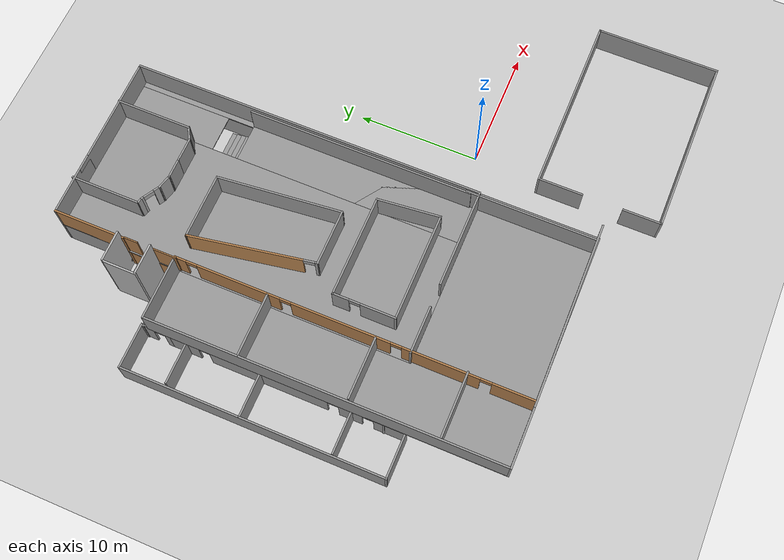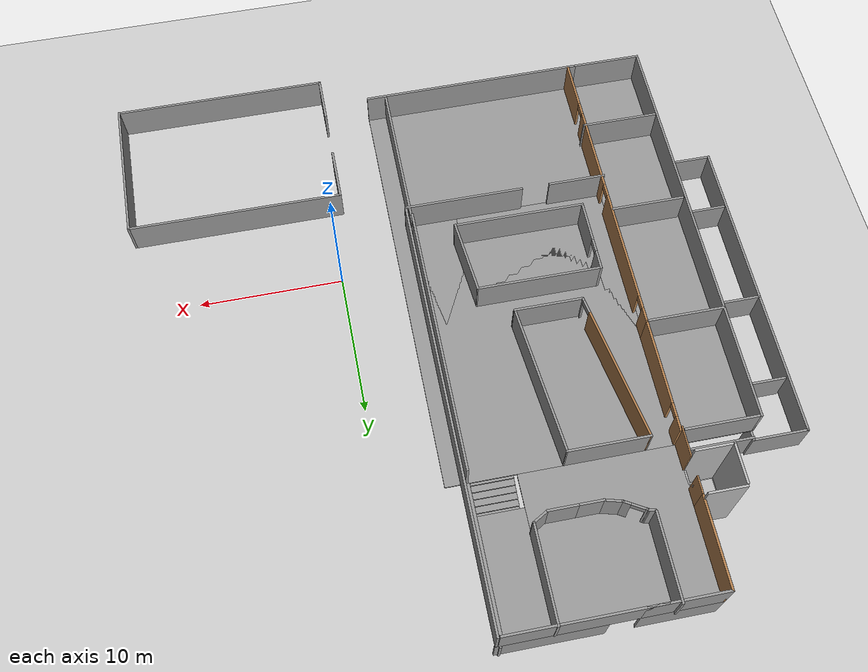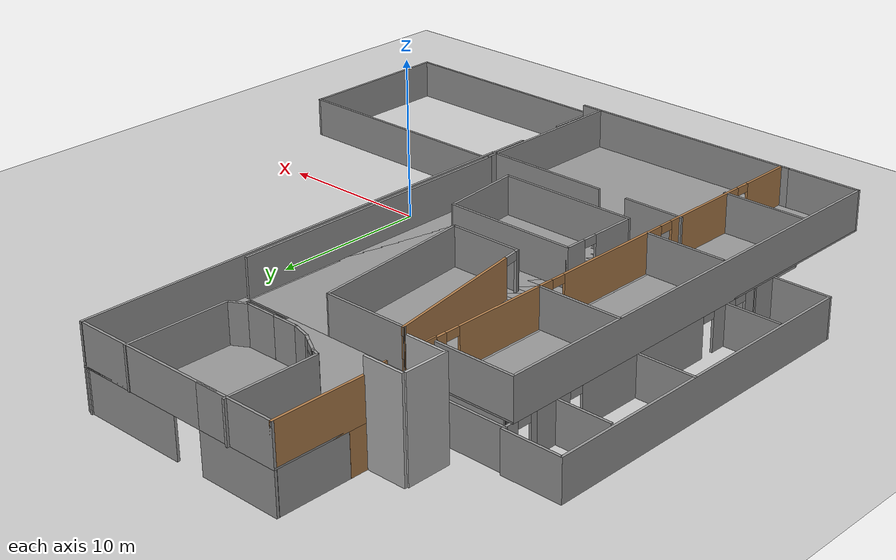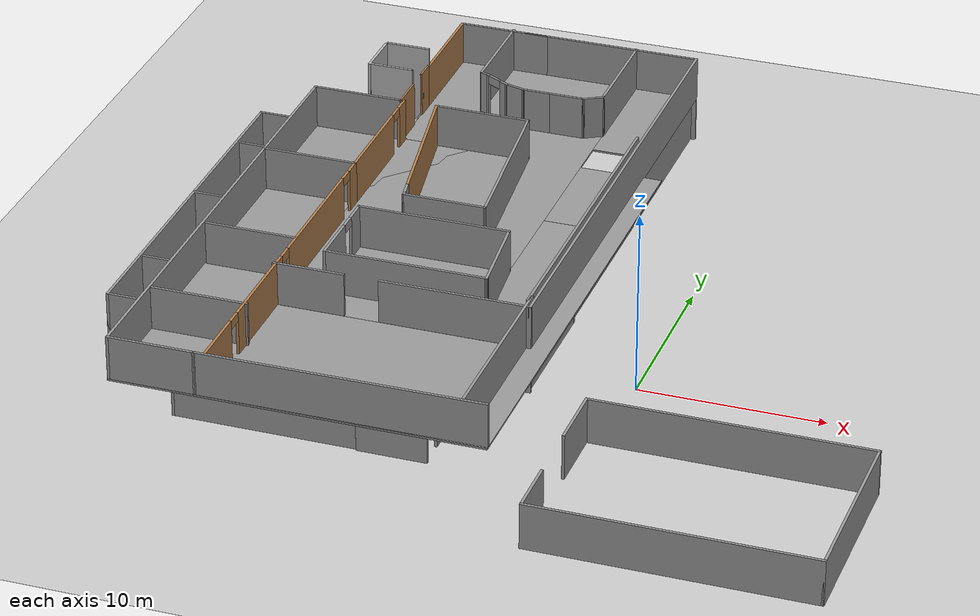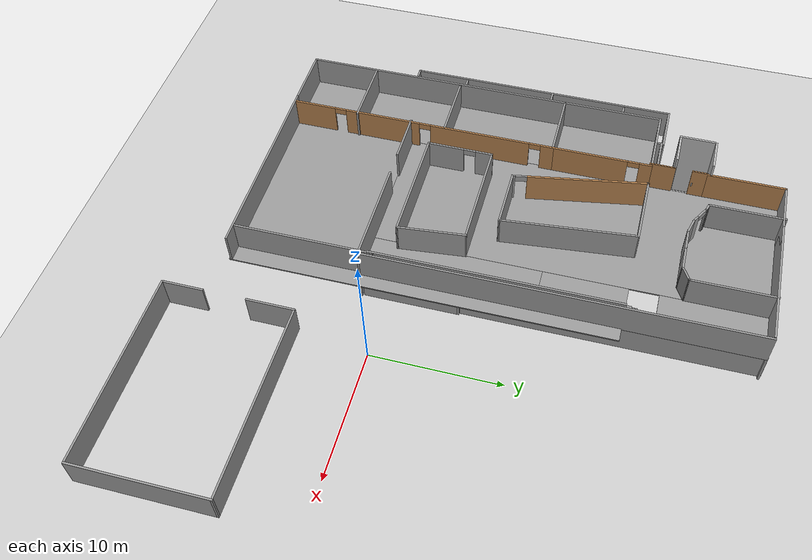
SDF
<?xml version="1.0" ?>
<sdf version="1.5">
  <world name="default">

    <!-- A global light source -->
    <include>
      <uri>model://sun</uri>
    </include>

    <!-- A ground plane -->
    <include>
      <uri>model://ground_plane</uri>
    </include>

    <!-- World plugin that publishes event messages.
         The topics used in these messages match up with topics used by the
         plugin in the elevator model below.
    -->
    <plugin filename="libSimEventsPlugin.so" name="elevator_event_plugin">
      <!-- Region on the ground floor, in front of the elevator -->
      <region>
        <name>region1</name>
        <volume>
          <min>-18.64 20.19 1.02</min>
          <max>-18.59 20.27 1.06</max>
        </volume>
      </region>

         <!-- Region on the ground floor inside the elevator-->
      <region>
        <name>region1_inside</name>
        <volume>
          <min>-19.7 19.1 0</min>
          <max>-19.1 19.8 1</max>
        </volume>
      </region>

          <!-- Region on the first floor inside the elevator-->
      <region>
        <name>region2_inside</name>
        <volume>
          <min>-19.7 19.1 2.58</min>
          <max>-19.1 19.8 2.8</max>
        </volume>
      </region>

      <!-- Region on the first floor, in front of the elevator -->
      <region>
        <name>region2</name>
        <volume>
          <min>-18.65 20.18 3.6</min>
          <max>-18.23 20.24 3.65</max>
        </volume>
      </region>

      <!-- Event publisher for ground floor-->
      <event>
        <name>region1_event</name>
        <type>occupied</type>
        <region>region1</region>
        <topic>~/elevator</topic>
        <msg_data>0</msg_data>
      </event>

      <!-- Event publisher for first floor-->
      <event>
        <name>region2_event</name>
        <type>occupied</type>
        <region>region2</region>

        <topic>~/elevator</topic>
        <msg_data>1</msg_data>
      </event>

      <!-- Event publisher up to first floor-->
      <event>
        <name>region2_1_event</name>
        <type>occupied</type>

        <region>region1_inside</region>
        <topic>~/elevator</topic>
        <msg_data>1</msg_data>
      </event>

       <!-- Event publisher down to ground floor-->
      <event>
        <name>region1_2_event</name>
        <type>occupied</type>
        <region>region2_inside</region>
        <topic>~/elevator</topic>
        <msg_data>0</msg_data>
      </event>
    </plugin>

    <!-- The elevator car -->
    <model name="elevator">
      <pose>-20 20 0.001 0 0 0</pose>
      <link name="link">
        <inertial>
          <mass>800</mass>
        </inertial>

        <collision name="floor_collision">
          <geometry>
            <box>
              <size>2.25 2.25 0.001</size>
            </box>
          </geometry>
        </collision>
        <visual name="floor_visual">
          <geometry>
            <box>
              <size>2.25 2.25 0.001</size>
            </box>
          </geometry>
        </visual>

        <collision name="wall1_collision_bot_in">
          <pose>0.06 0.25 1.125 0 0 0</pose>
          <geometry>
            <box>
              <size>0.01 0.09 0.36</size>
            </box>
          </geometry>
        </collision>
        <visual name="wall1_visual_bot_in">
          <pose>1.0 1.25 1.125 0 0 1.577</pose>
          <geometry>
            <box>
              <size>0.01 0.09 0.36</size>
            </box>
          </geometry>
          <material>
                      <script>
            <uri>model://elevator_shaft/materials/scripts</uri>
            <uri>model://elevator_shaft/materials/textures</uri>
            <name>Up_down/Diffuse</name>
          </script>
          </material>
        </visual>

        <!-- wall1_collision is the wall to the right of the door, when
             facing the door -->

        <!-- wall2_collision is the wall to the left of the door, when
             facing the door -->

      </link>

      <link name="door">
        <pose>1.0745 -0.5 1.125 0 0 0</pose>
        <collision name="collision">
          <geometry>
            <box>
              <size>0.08 1.2 2.25</size>
            </box>
          </geometry>
        </collision>
        <visual name="visual">
        <material>
          <script>
            <uri>model://elevator_door/materials/scripts</uri>
            <uri>model://elevator_door/materials/textures</uri>
            <name>Elevator_door/Picture</name>
          </script>
          <shader type='pixel'>
            <normal_map>__default__</normal_map>
          </shader>
          <ambient>1 1 1 1</ambient>
          <diffuse>1 1 1 1</diffuse>
          <specular>0 0 0 1</specular>
          <emissive>0 0 0 1</emissive>
        </material>
          <geometry>
            <box>
              <size>0.08 1.2 2.25</size>
            </box>
          </geometry>
        </visual>
      </link>

      <joint name="door" type="prismatic">
        <parent>link</parent>
        <child>door</child>
        <axis>
          <xyz>0 1 0</xyz>
          <limit>
            <lower>0</lower>
            <upper>1.19</upper>
            <effort>0.525</effort>
          </limit>

          <dynamics>
            <damping>1</damping>
          </dynamics>
        </axis>
      </joint>

      <joint name="lift" type="prismatic">
        <parent>world</parent>
        <child>link</child>
        <axis>
          <xyz>0 0 1</xyz>
          <limit>
            <lower>0</lower>
            <upper>10</upper>
            <effort>100000</effort>
          </limit>

          <dynamics>
            <damping>50</damping>
          </dynamics>
        </axis>
        <physics>
          <ode>
            <implicit_spring_damper>1</implicit_spring_damper>
          </ode>
        </physics>
      </joint>

      <!-- Plugin to control the elevator -->
      <plugin filename="libElevatorPlugin.so" name="elevator_plugin">
        <lift_joint>elevator::lift</lift_joint>
        <door_joint>elevator::door</door_joint>
        <floor_height>2.675</floor_height>

        <!-- Time the elevator door will stay open in seconds -->
        <door_wait_time>8</door_wait_time>

        <!-- This topic is used to control the elevator -->
        <topic>~/elevator</topic>
      </plugin>
    </model>

    <!-- Elevator shaft -->
    <model name="elevator_shaft">
        <pose>-20 20 0.00 0 0 0</pose>
      <static>true</static>
      <link name="link">
        <collision name="shaft_wall1_collision">
          <pose>0 1.45 3 0 0 0</pose>
          <geometry>
            <box>
              <size>2.5 0.15 6</size>
            </box>
          </geometry>
        </collision>
        <visual name="shaft_wall1_visual">
          <pose>0 1.45 3 0 0 0</pose>
          <geometry>
            <box>
              <size>2.5 0.15 6</size>
            </box>
          </geometry>
        </visual>

        <collision name="shaft_wall2_collision">
          <pose>0 -1.25 3 0 0 0</pose>
          <geometry>
            <box>
              <size>2.5 0.15 6</size>
            </box>
          </geometry>
        </collision>
        <visual name="shaft_wall2_visual">
          <pose>0 -1.25 3 0 0 0</pose>
          <geometry>
            <box>
              <size>2.5 0.15 6</size>
            </box>
          </geometry>
        </visual>

        <collision name="shaft_wall3_collision">
          <pose>-1.25 0 3 0 0 0</pose>
          <geometry>
            <box>
              <size>0.15 2.7 6</size>
            </box>
          </geometry>
        </collision>
        <visual name="shaft_wall3_visual">
          <pose>-1.25 0 3 0 0 0</pose>
          <geometry>
            <box>
              <size>0.15 2.7 6</size>
            </box>
          </geometry>
        </visual>

        <collision name="floor0_collision">
          <pose>1.19 0 0.001 0 0 0</pose>
          <geometry>
            <box>
              <size>0.12 2.5 0.001</size>
            </box>
          </geometry>
        </collision>
        <visual name="floor0_visual">
          <pose>1.19 0 0.001 0 0 0</pose>
          <geometry>
            <box>
              <size>0.12 2.5 0.001</size>
            </box>
          </geometry>
        </visual>

        <collision name="floor1_collision">
          <pose>1.19 0 2.525 0 0 0</pose>
          <geometry>
            <box>
              <size>0.12 2.5 0.15</size>
            </box>
          </geometry>
        </collision>
        <visual name="floor1_visual">
          <pose>1.19 0 2.525 0 0 0</pose>
          <geometry>
            <box>
              <size>0.12 2.5 0.15</size>
            </box>
          </geometry>
        </visual>
      </link>
    </model>

  <model name='elevator_2.5'>
    <pose frame=''>-18.75 20 0 0 -0 0</pose>
    <link name='Wall_0'>
      <collision name='Wall_0_Collision'>
        <geometry>
          <box>
            <size>1.4 0.15 2.5</size>
          </box>
        </geometry>
        <pose frame=''>0 0 1.25 0 -0 0</pose>
      </collision>
      <visual name='Wall_0_Visual'>
        <pose frame=''>0 0 1.25 0 -0 0</pose>
          <meta>
            <layer>0</layer>
          </meta>
        <geometry>
          <box>
            <size>1.4 0.15 2.5</size>
          </box>
        </geometry>
       <material>
            <script>
              <name>Gazebo/Wood </name>
            </script>
          </material>
      </visual>
      <pose frame=''>0 -1.875 0 0 0 -1.5708</pose>
    </link>

  <pose frame=''> 0.02 -1.1 1.15 0 -0 0</pose>
   <!-- wall2_collision is the wall to the left of the door, when
             facing the door -->

    <link name='Wall_2'>
      <collision name='Wall_2_Collision'>
        <geometry>
          <box>
            <size>1.4 0.15 2.5</size>
          </box>
        </geometry>
        <pose frame=''>0 0 1.25 0 -0 0</pose>
      </collision>
      <visual name='Wall_2_Visual'>
        <pose frame=''>0 0 1.25 0 -0 0</pose>
        <geometry>
          <box>
            <size>1.4 0.15 2.5</size>
          </box>
        </geometry>
        <material>
            <script>
              <name>Gazebo/Wood </name>
            </script>
          </material>
      </visual>
      <pose frame=''>0 1.875 0 0 0 -1.5708</pose>
    </link>

    <link name="right_elevator_wall_floor_0">
    <collision name="wall1_collision">
          <pose>0.0 0.6 1.125 0 0 0</pose>
          <geometry>
            <box>
              <size>0.1 1.15 2.85</size>
            </box>
          </geometry>
        </collision>
        <visual name="wall1_visual">
          <pose>0.0 0.6 1.125 0 0 0</pose>
          <geometry>
            <box>
              <size>0.1 1.15 2.85</size>
            </box>
          </geometry>
          <material>
            <script>
              <name>Gazebo/Wood </name>
            </script>
          </material>
        </visual>

             <collision name="wall1_collision_bot">
          <pose>0.06 0.3 1.125 0 0 0</pose>
          <geometry>
            <box>
              <size>0.01 0.09 0.36</size>
            </box>
          </geometry>
        </collision>
        <visual name="wall1_visual_bot">
          <pose>0.06 0.25 1.125 0 0 0</pose>
          <geometry>
            <box>
              <size>0.01 0.09 0.36</size>
            </box>
          </geometry>
          <material>
                      <script>
            <uri>model://elevator_shaft/materials/scripts</uri>
            <uri>model://elevator_shaft/materials/textures</uri>
            <name>Up_down/Diffuse</name>
          </script>
          </material>
        </visual>

    </link>

    <static>1</static>
  </model>

  <model name='Building_37'>
    <pose frame=''>-14.375 11 0 0 -0 0</pose>
    <link name='Floor_0'>
      <pose frame=''>2.5 1.3455 2.5 0 -0 0</pose>
      <visual name='Floor_0_Visual_0'>
        <pose frame=''>-1.7875 0.15 0.05 0 -0 0</pose>
          <meta>
            <layer>1</layer>
          </meta>
        <geometry>
          <box>
            <size>10.325 29.15 0.1</size>
          </box>
        </geometry>
        <material>
          <script>
            <uri>file://media/materials/scripts/gazebo.material</uri>
            <name>Gazebo/Grey</name>
          </script>
          <ambient>1 1 1 1</ambient>
        </material>
      </visual>
      <collision name='Floor_0_Collision_0'>
        <geometry>
          <box>
            <size>10.325 29.15 0.1</size>
          </box>
        </geometry>
        <pose frame=''>-1.7875 0.15 0.05 0 -0 0</pose>
      </collision>
      <visual name='Floor_0_Visual_1'>
        <pose frame=''>5.1625 -8.0 0.05 0 -0 0</pose>
          <meta>
            <layer>1</layer>
          </meta>
        <geometry>
          <box>
            <size>3.575 12.85 0.1</size>
          </box>
        </geometry>
        <material>
          <script>
            <uri>file://media/materials/scripts/gazebo.material</uri>
            <name>Gazebo/Grey</name>
          </script>
          <ambient>1 1 1 1</ambient>
        </material>
      </visual>
      <collision name='Floor_0_Collision_1'>
        <geometry>
          <box>
            <size>3.575 12.85 0.1</size>
          </box>
        </geometry>
        <pose frame=''>5.1625 -8.0 0.05 0 -0 0</pose>
      </collision>
      <visual name='Floor_0_Visual_2'>
        <pose frame=''>6.6625 6.567 0.05 0 -0 0</pose>
          <meta>
            <layer>1</layer>
          </meta>
        <geometry>
          <box>
            <size>0.575 16.325 0.1</size>
          </box>
        </geometry>
        <material>
          <script>
            <uri>file://media/materials/scripts/gazebo.material</uri>
            <name>Gazebo/Grey</name>
          </script>
          <ambient>1 1 1 1</ambient>
        </material>
      </visual>
      <collision name='Floor_0_Collision_2'>
        <geometry>
          <box>
            <size>0.575 16.325 0.1</size>
          </box>
        </geometry>
        <pose frame=''>6.6625 6.567 0.05 0 -0 0</pose>
      </collision>
      <visual name='Floor_0_Visual_3'>
        <pose frame=''>4.875 10.817 0.05 0 -0 0</pose>
          <meta>
            <layer>1</layer>
          </meta>
        <geometry>
          <box>
            <size>3 7.825 0.1</size>
          </box>
        </geometry>
        <material>
          <script>
            <uri>file://media/materials/scripts/gazebo.material</uri>
            <name>Gazebo/Grey</name>
          </script>
          <ambient>1 1 1 1</ambient>
        </material>
      </visual>
      <collision name='Floor_0_Collision_3'>
        <geometry>
          <box>
            <size>3 7.825 0.1</size>
          </box>
        </geometry>
        <pose frame=''>4.875 10.817 0.05 0 -0 0</pose>
      </collision>
    </link>
    <link name='Stairs_1'>
      <visual name='Stairs_1_Visual_0'>
        <pose frame=''>7.375 8.0375 0.0625 0 -0 0</pose>
          <meta>
            <layer>2</layer>
          </meta>
        <geometry>
          <box>
            <size>3 0.425 0.125</size>
          </box>
        </geometry>
        <material>
          <script>
            <uri>file://media/materials/scripts/gazebo.material</uri>
            <name>Gazebo/Grey</name>
          </script>
          <ambient>1 1 1 1</ambient>
        </material>
      </visual>
      <collision name='Stairs_1_Collision_0'>
        <geometry>
          <box>
            <size>3 0.425 0.125</size>
          </box>
        </geometry>
        <pose frame=''>7.375 8.0375 0.0625 0 -0 0</pose>
      </collision>
      <visual name='Stairs_1_Visual_1'>
        <pose frame=''>7.375 7.6125 0.1875 0 -0 0</pose>
          <meta>
            <layer>2</layer>
          </meta>
        <geometry>
          <box>
            <size>3 0.425 0.125</size>
          </box>
        </geometry>
        <material>
          <script>
            <uri>file://media/materials/scripts/gazebo.material</uri>
            <name>Gazebo/Grey</name>
          </script>
          <ambient>1 1 1 1</ambient>
        </material>
      </visual>
      <collision name='Stairs_1_Collision_1'>
        <geometry>
          <box>
            <size>3 0.425 0.125</size>
          </box>
        </geometry>
        <pose frame=''>7.375 7.6125 0.1875 0 -0 0</pose>
      </collision>
      <visual name='Stairs_1_Visual_2'>
        <pose frame=''>7.375 7.1875 0.3125 0 -0 0</pose>
          <meta>
            <layer>2</layer>
          </meta>
        <geometry>
          <box>
            <size>3 0.425 0.125</size>
          </box>
        </geometry>
        <material>
          <script>
            <uri>file://media/materials/scripts/gazebo.material</uri>
            <name>Gazebo/Grey</name>
          </script>
          <ambient>1 1 1 1</ambient>
        </material>
      </visual>
      <collision name='Stairs_1_Collision_2'>
        <geometry>
          <box>
            <size>3 0.425 0.125</size>
          </box>
        </geometry>
        <pose frame=''>7.375 7.1875 0.3125 0 -0 0</pose>
      </collision>
      <visual name='Stairs_1_Visual_3'>
        <pose frame=''>7.375 6.7625 0.4375 0 -0 0</pose>
          <meta>
            <layer>2</layer>
          </meta>
        <geometry>
          <box>
            <size>3 0.425 0.125</size>
          </box>
        </geometry>
        <material>
          <script>
            <uri>file://media/materials/scripts/gazebo.material</uri>
            <name>Gazebo/Grey</name>
          </script>
          <ambient>1 1 1 1</ambient>
        </material>
      </visual>
      <collision name='Stairs_1_Collision_3'>
        <geometry>
          <box>
            <size>3 0.425 0.125</size>
          </box>
        </geometry>
        <pose frame=''>7.375 6.7625 0.4375 0 -0 0</pose>
      </collision>
      <visual name='Stairs_1_Visual_4'>
        <pose frame=''>7.375 6.3375 0.5625 0 -0 0</pose>
          <meta>
            <layer>2</layer>
          </meta>
        <geometry>
          <box>
            <size>3 0.425 0.125</size>
          </box>
        </geometry>
        <material>
          <script>
            <uri>file://media/materials/scripts/gazebo.material</uri>
            <name>Gazebo/Grey</name>
          </script>
          <ambient>1 1 1 1</ambient>
        </material>
      </visual>
      <collision name='Stairs_1_Collision_4'>
        <geometry>
          <box>
            <size>3 0.425 0.125</size>
          </box>
        </geometry>
        <pose frame=''>7.375 6.3375 0.5625 0 -0 0</pose>
      </collision>
      <visual name='Stairs_1_Visual_5'>
        <pose frame=''>7.375 5.9125 0.6875 0 -0 0</pose>
          <meta>
            <layer>2</layer>
          </meta>
        <geometry>
          <box>
            <size>3 0.425 0.125</size>
          </box>
        </geometry>
        <material>
          <script>
            <uri>file://media/materials/scripts/gazebo.material</uri>
            <name>Gazebo/Grey</name>
          </script>
          <ambient>1 1 1 1</ambient>
        </material>
      </visual>
      <collision name='Stairs_1_Collision_5'>
        <geometry>
          <box>
            <size>3 0.425 0.125</size>
          </box>
        </geometry>
        <pose frame=''>7.375 5.9125 0.6875 0 -0 0</pose>
      </collision>
      <visual name='Stairs_1_Visual_6'>
        <pose frame=''>7.375 5.4875 0.8125 0 -0 0</pose>
          <meta>
            <layer>2</layer>
          </meta>
        <geometry>
          <box>
            <size>3 0.425 0.125</size>
          </box>
        </geometry>
        <material>
          <script>
            <uri>file://media/materials/scripts/gazebo.material</uri>
            <name>Gazebo/Grey</name>
          </script>
          <ambient>1 1 1 1</ambient>
        </material>
      </visual>
      <collision name='Stairs_1_Collision_6'>
        <geometry>
          <box>
            <size>3 0.425 0.125</size>
          </box>
        </geometry>
        <pose frame=''>7.375 5.4875 0.8125 0 -0 0</pose>
      </collision>
      <visual name='Stairs_1_Visual_7'>
        <pose frame=''>7.375 5.0625 0.9375 0 -0 0</pose>
          <meta>
            <layer>2</layer>
          </meta>
        <geometry>
          <box>
            <size>3 0.425 0.125</size>
          </box>
        </geometry>
        <material>
          <script>
            <uri>file://media/materials/scripts/gazebo.material</uri>
            <name>Gazebo/Grey</name>
          </script>
          <ambient>1 1 1 1</ambient>
        </material>
      </visual>
      <collision name='Stairs_1_Collision_7'>
        <geometry>
          <box>
            <size>3 0.425 0.125</size>
          </box>
        </geometry>
        <pose frame=''>7.375 5.0625 0.9375 0 -0 0</pose>
      </collision>
      <visual name='Stairs_1_Visual_8'>
        <pose frame=''>7.375 4.6375 1.0625 0 -0 0</pose>
          <meta>
            <layer>2</layer>
          </meta>
        <geometry>
          <box>
            <size>3 0.425 0.125</size>
          </box>
        </geometry>
        <material>
          <script>
            <uri>file://media/materials/scripts/gazebo.material</uri>
            <name>Gazebo/Grey</name>
          </script>
          <ambient>1 1 1 1</ambient>
        </material>
      </visual>
      <collision name='Stairs_1_Collision_8'>
        <geometry>
          <box>
            <size>3 0.425 0.125</size>
          </box>
        </geometry>
        <pose frame=''>7.375 4.6375 1.0625 0 -0 0</pose>
      </collision>
      <visual name='Stairs_1_Visual_9'>
        <pose frame=''>7.375 4.2125 1.1875 0 -0 0</pose>
          <meta>
            <layer>2</layer>
          </meta>
        <geometry>
          <box>
            <size>3 0.425 0.125</size>
          </box>
        </geometry>
        <material>
          <script>
            <uri>file://media/materials/scripts/gazebo.material</uri>
            <name>Gazebo/Grey</name>
          </script>
          <ambient>1 1 1 1</ambient>
        </material>
      </visual>
      <collision name='Stairs_1_Collision_9'>
        <geometry>
          <box>
            <size>3 0.425 0.125</size>
          </box>
        </geometry>
        <pose frame=''>7.375 4.2125 1.1875 0 -0 0</pose>
      </collision>
      <visual name='Stairs_1_Visual_10'>
        <pose frame=''>7.375 3.7875 1.3125 0 -0 0</pose>
          <meta>
            <layer>2</layer>
          </meta>
        <geometry>
          <box>
            <size>3 0.425 0.125</size>
          </box>
        </geometry>
        <material>
          <script>
            <uri>file://media/materials/scripts/gazebo.material</uri>
            <name>Gazebo/Grey</name>
          </script>
          <ambient>1 1 1 1</ambient>
        </material>
      </visual>
      <collision name='Stairs_1_Collision_10'>
        <geometry>
          <box>
            <size>3 0.425 0.125</size>
          </box>
        </geometry>
        <pose frame=''>7.375 3.7875 1.3125 0 -0 0</pose>
      </collision>
      <visual name='Stairs_1_Visual_11'>
        <pose frame=''>7.375 3.3625 1.4375 0 -0 0</pose>
          <meta>
            <layer>2</layer>
          </meta>
        <geometry>
          <box>
            <size>3 0.425 0.125</size>
          </box>
        </geometry>
        <material>
          <script>
            <uri>file://media/materials/scripts/gazebo.material</uri>
            <name>Gazebo/Grey</name>
          </script>
          <ambient>1 1 1 1</ambient>
        </material>
      </visual>
      <collision name='Stairs_1_Collision_11'>
        <geometry>
          <box>
            <size>3 0.425 0.125</size>
          </box>
        </geometry>
        <pose frame=''>7.375 3.3625 1.4375 0 -0 0</pose>
      </collision>
      <visual name='Stairs_1_Visual_12'>
        <pose frame=''>7.375 2.9375 1.5625 0 -0 0</pose>
          <meta>
            <layer>2</layer>
          </meta>
        <geometry>
          <box>
            <size>3 0.425 0.125</size>
          </box>
        </geometry>
        <material>
          <script>
            <uri>file://media/materials/scripts/gazebo.material</uri>
            <name>Gazebo/Grey</name>
          </script>
          <ambient>1 1 1 1</ambient>
        </material>
      </visual>
      <collision name='Stairs_1_Collision_12'>
        <geometry>
          <box>
            <size>3 0.425 0.125</size>
          </box>
        </geometry>
        <pose frame=''>7.375 2.9375 1.5625 0 -0 0</pose>
      </collision>
      <visual name='Stairs_1_Visual_13'>
        <pose frame=''>7.375 2.5125 1.6875 0 -0 0</pose>
          <meta>
            <layer>2</layer>
          </meta>
        <geometry>
          <box>
            <size>3 0.425 0.125</size>
          </box>
        </geometry>
        <material>
          <script>
            <uri>file://media/materials/scripts/gazebo.material</uri>
            <name>Gazebo/Grey</name>
          </script>
          <ambient>1 1 1 1</ambient>
        </material>
      </visual>
      <collision name='Stairs_1_Collision_13'>
        <geometry>
          <box>
            <size>3 0.425 0.125</size>
          </box>
        </geometry>
        <pose frame=''>7.375 2.5125 1.6875 0 -0 0</pose>
      </collision>
      <visual name='Stairs_1_Visual_14'>
        <pose frame=''>7.375 2.0875 1.8125 0 -0 0</pose>
          <meta>
            <layer>2</layer>
          </meta>
        <geometry>
          <box>
            <size>3 0.425 0.125</size>
          </box>
        </geometry>
        <material>
          <script>
            <uri>file://media/materials/scripts/gazebo.material</uri>
            <name>Gazebo/Grey</name>
          </script>
          <ambient>1 1 1 1</ambient>
        </material>
      </visual>
      <collision name='Stairs_1_Collision_14'>
        <geometry>
          <box>
            <size>3 0.425 0.125</size>
          </box>
        </geometry>
        <pose frame=''>7.375 2.0875 1.8125 0 -0 0</pose>
      </collision>
      <visual name='Stairs_1_Visual_15'>
        <pose frame=''>7.375 1.6625 1.9375 0 -0 0</pose>
          <meta>
            <layer>2</layer>
          </meta>
        <geometry>
          <box>
            <size>3 0.425 0.125</size>
          </box>
        </geometry>
        <material>
          <script>
            <uri>file://media/materials/scripts/gazebo.material</uri>
            <name>Gazebo/Grey</name>
          </script>
          <ambient>1 1 1 1</ambient>
        </material>
      </visual>
      <collision name='Stairs_1_Collision_15'>
        <geometry>
          <box>
            <size>3 0.425 0.125</size>
          </box>
        </geometry>
        <pose frame=''>7.375 1.6625 1.9375 0 -0 0</pose>
      </collision>
      <visual name='Stairs_1_Visual_16'>
        <pose frame=''>7.375 1.2375 2.0625 0 -0 0</pose>
          <meta>
            <layer>2</layer>
          </meta>
        <geometry>
          <box>
            <size>3 0.425 0.125</size>
          </box>
        </geometry>
        <material>
          <script>
            <uri>file://media/materials/scripts/gazebo.material</uri>
            <name>Gazebo/Grey</name>
          </script>
          <ambient>1 1 1 1</ambient>
        </material>
      </visual>
      <collision name='Stairs_1_Collision_16'>
        <geometry>
          <box>
            <size>3 0.425 0.125</size>
          </box>
        </geometry>
        <pose frame=''>7.375 1.2375 2.0625 0 -0 0</pose>
      </collision>
      <visual name='Stairs_1_Visual_17'>
        <pose frame=''>7.375 0.8125 2.1875 0 -0 0</pose>
          <meta>
            <layer>2</layer>
          </meta>
        <geometry>
          <box>
            <size>3 0.425 0.125</size>
          </box>
        </geometry>
        <material>
          <script>
            <uri>file://media/materials/scripts/gazebo.material</uri>
            <name>Gazebo/Grey</name>
          </script>
          <ambient>1 1 1 1</ambient>
        </material>
      </visual>
      <collision name='Stairs_1_Collision_17'>
        <geometry>
          <box>
            <size>3 0.425 0.125</size>
          </box>
        </geometry>
        <pose frame=''>7.375 0.8125 2.1875 0 -0 0</pose>
      </collision>
      <visual name='Stairs_1_Visual_18'>
        <pose frame=''>7.375 0.3875 2.3125 0 -0 0</pose>
          <meta>
            <layer>2</layer>
          </meta>
        <geometry>
          <box>
            <size>3 0.425 0.125</size>
          </box>
        </geometry>
        <material>
          <script>
            <uri>file://media/materials/scripts/gazebo.material</uri>
            <name>Gazebo/Grey</name>
          </script>
          <ambient>1 1 1 1</ambient>
        </material>
      </visual>
      <collision name='Stairs_1_Collision_18'>
        <geometry>
          <box>
            <size>3 0.425 0.125</size>
          </box>
        </geometry>
        <pose frame=''>7.375 0.3875 2.3125 0 -0 0</pose>
      </collision>
      <visual name='Stairs_1_Visual_19'>
        <pose frame=''>7.375 -0.037501 2.4375 0 -0 0</pose>
          <meta>
            <layer>2</layer>
          </meta>
        <geometry>
          <box>
            <size>3 0.425 0.125</size>
          </box>
        </geometry>
        <material>
          <script>
            <uri>file://media/materials/scripts/gazebo.material</uri>
            <name>Gazebo/Grey</name>
          </script>
          <ambient>1 1 1 1</ambient>
        </material>
      </visual>
      <collision name='Stairs_1_Collision_19'>
        <geometry>
          <box>
            <size>3 0.425 0.125</size>
          </box>
        </geometry>
        <pose frame=''>7.375 -0.037501 2.4375 0 -0 0</pose>
      </collision>
    </link>

    <link name='Wall_27'>
      <collision name='Wall_27_Collision'>
        <geometry>
          <box>
            <size>6.9 0.15 2.5</size>
          </box>
        </geometry>
        <pose frame=''>0 0 1.25 0 -0 0</pose>
      </collision>
      <visual name='Wall_27_Visual'>
        <pose frame=''>0 0 1.25 0 -0 0</pose>
        <geometry>
          <box>
            <size>6.9 0.15 2.5</size>
          </box>
        </geometry>
        <material>
          <script>
            <uri>file://media/materials/scripts/gazebo.material</uri>
            <name>Gazebo/Grey</name>
          </script>
          <ambient>1 1 1 1</ambient>
        </material>
      </visual>
      <pose frame=''>-6 -13 0 0 -0 0</pose>
    </link>
    <link name='Wall_28'>
      <collision name='Wall_28_Collision'>
        <geometry>
          <box>
            <size>3.15 0.15 2.5</size>
          </box>
        </geometry>
        <pose frame=''>0 0 1.25 0 -0 0</pose>
      </collision>
      <visual name='Wall_28_Visual'>
        <pose frame=''>0 0 1.25 0 -0 0</pose>
        <geometry>
          <box>
            <size>3.15 0.15 2.5</size>
          </box>
        </geometry>
        <material>
          <script>
            <uri>file://media/materials/scripts/gazebo.material</uri>
            <name>Gazebo/Grey</name>
          </script>
          <ambient>1 1 1 1</ambient>
        </material>
      </visual>
      <pose frame=''>-2.625 -14.5 0 0 0 -1.5708</pose>
    </link>
    <link name='Wall_30'>
      <collision name='Wall_30_Collision'>
        <geometry>
          <box>
            <size>10.15 0.15 2.5</size>
          </box>
        </geometry>
        <pose frame=''>0 0 1.25 0 -0 0</pose>
      </collision>
      <visual name='Wall_30_Visual'>
        <pose frame=''>0 0 1.25 0 -0 0</pose>
        <geometry>
          <box>
            <size>10.15 0.15 2.5</size>
          </box>
        </geometry>
        <material>
          <script>
            <uri>file://media/materials/scripts/gazebo.material</uri>
            <name>Gazebo/Grey</name>
          </script>
          <ambient>1 1 1 1</ambient>
        </material>
      </visual>
      <pose frame=''>4.375 -13 0 0 -0 3.14159</pose>
    </link>
    <link name='Wall_31'>
      <collision name='Wall_31_Collision'>
        <geometry>
          <box>
            <size>3.15 0.15 2.5</size>
          </box>
        </geometry>
        <pose frame=''>0 0 1.25 0 -0 0</pose>
      </collision>
      <visual name='Wall_31_Visual'>
        <pose frame=''>0 0 1.25 0 -0 0</pose>
        <geometry>
          <box>
            <size>3.15 0.15 2.5</size>
          </box>
        </geometry>
        <material>
          <script>
            <uri>file://media/materials/scripts/gazebo.material</uri>
            <name>Gazebo/Grey</name>
          </script>
          <ambient>1 1 1 1</ambient>
        </material>
      </visual>
      <pose frame=''>-0.625 -14.5 0 0 0 -1.5708</pose>
    </link>
    <link name='Wall_33'>
      <collision name='Wall_33_Collision'>
        <geometry>
          <box>
            <size>5.9 0.15 2.5</size>
          </box>
        </geometry>
        <pose frame=''>0 0 1.25 0 -0 0</pose>
      </collision>
      <visual name='Wall_33_Visual'>
        <pose frame=''>0 0 1.25 0 -0 0</pose>
          <meta>
            <layer>3</layer>
          </meta>
        <geometry>
          <box>
            <size>5.9 0.15 2.5</size>
          </box>
        </geometry>
       <material>
            <script>
              <name>Gazebo/Wood </name>
            </script>
          </material>
      </visual>
      <pose frame=''>-4.375 13.125 2.5 0 0 -1.5708</pose>
    </link>

    <pose frame=''> -4.35 9.85 3.7 0 -0 0</pose>
    <link name="right_elevator_wall_floor_1">
    <collision name="wall1_collision">
          <pose>-4.32 9.6 3.7 0 -0 0</pose>
          <geometry>
            <box>
              <size>0.1 1.15 2.85</size>
            </box>
          </geometry>
        </collision>
        <visual name="wall1_visual">
          <pose>-4.35 9.6 3.7 0 -0 0</pose>
          <geometry>
            <box>
              <size>0.1 1.15 2.85</size>
            </box>
          </geometry>
          <material>
            <script>
              <name>Gazebo/Wood </name>
            </script>
          </material>
        </visual>

             <collision name="wall1_collision_bot">
          <pose>-4.3 9.2 3.7 0 -0 0</pose>
          <geometry>
            <box>
              <size>0.01 0.09 0.36</size>
            </box>
          </geometry>
        </collision>
        <visual name="wall1_visual_bot">
          <pose>-4.3 9.2 3.7 0 -0 0</pose>
          <geometry>
            <box>
              <size>0.01 0.09 0.36</size>
            </box>
          </geometry>
          <material>
                      <script>
            <uri>model://elevator_shaft/materials/scripts</uri>
            <uri>model://elevator_shaft/materials/textures</uri>
            <name>Up_down/Diffuse</name>
          </script>
          </material>
        </visual>

</link>
  <link name="left_elevator_wall_floor_1">
    <collision name="wall1_collision_l">
          <pose>-4.32 6.8 3.7 0 -0 0</pose>
          <geometry>
            <box>
              <size>0.1 2.0 2.85</size>
            </box>
          </geometry>
        </collision>
        <visual name="wall1_visual_l">
          <pose>-4.35 6.8 3.7 0 -0 0</pose>
          <geometry>
            <box>
              <size>0.1 2.0 2.85</size>
            </box>
          </geometry>
          <material>
            <script>
              <name>Gazebo/Wood </name>
            </script>
          </material>
        </visual>
  </link>

    <link name='Wall_34'>
      <collision name='Wall_34_Collision'>
        <geometry>
          <box>
            <size>5.15 0.15 2.5</size>
          </box>
        </geometry>
        <pose frame=''>0 0 1.25 0 -0 0</pose>
      </collision>
      <visual name='Wall_34_Visual'>
        <pose frame=''>0 0 1.25 0 -0 0</pose>
          <meta>
            <layer>3</layer>
          </meta>
        <geometry>
          <box>
            <size>5.15 0.15 2.5</size>
          </box>
        </geometry>
        <material>
          <script>
            <uri>file://media/materials/scripts/gazebo.material</uri>
            <name>Gazebo/Grey</name>
          </script>
          <ambient>1 1 1 1</ambient>
        </material>
      </visual>
      <pose frame=''>-1.875 16 2.5 0 -0 0</pose>
    </link>
    <link name='Wall_35'>
      <collision name='Wall_35_Collision'>
        <geometry>
          <box>
            <size>6.9 0.15 2.5</size>
          </box>
        </geometry>
        <pose frame=''>0 0 1.25 0 -0 0</pose>
      </collision>
      <visual name='Wall_35_Visual'>
        <pose frame=''>-1.70 0 1.25 0 -0 0</pose>
          <meta>
            <layer>3</layer>
          </meta>
        <geometry>
          <box>
            <size>9.9 0.15 2.5</size>
          </box>
        </geometry>
        <material>
          <script>
            <uri>file://media/materials/scripts/gazebo.material</uri>
            <name>Gazebo/Grey</name>
          </script>
          <ambient>1 1 1 1</ambient>
        </material>
      </visual>
      <pose frame=''>6 16 2.5 0 -0 0</pose>
    </link>
      <pose frame=''> -4.32 7.95 3.7 0 -0 0</pose>
   <!-- wall2_collision is the wall to the left of the door, when
             facing the door -->

    <link name='Wall_38'>
      <pose frame=''>-1.5 1 2.5 0 0 -1.39755</pose>
      <visual name='Wall_38_Visual_0'>
        <pose frame=''>-0.58726 0 1.25 0 -0 0</pose>
          <meta>
            <layer>3</layer>
          </meta>
        <geometry>
          <box>
            <size>9.12745 0.15 2.5</size>
          </box>
        </geometry>
        <material>
          <script>
            <uri>file://media/materials/scripts/gazebo.material</uri>
            <name>Gazebo/Wood</name>
          </script>
          <ambient>1 1 1 1</ambient>
        </material>
      </visual>
      <collision name='Wall_38_Collision_0'>
        <geometry>
          <box>
            <size>9.12745 0.15 2.5</size>
          </box>
        </geometry>
        <pose frame=''>-0.58726 0 1.25 0 -0 0</pose>
      </collision>
      <visual name='Wall_38_Visual_1'>
        <pose frame=''>5.01372 0 1.25 0 -0 0</pose>
          <meta>
            <layer>3</layer>
          </meta>
        <geometry>
          <box>
            <size>0.274521 0.15 2.5</size>
          </box>
        </geometry>
        <material>
          <script>
            <uri>file://media/materials/scripts/gazebo.material</uri>
            <name>Gazebo/Grey</name>
          </script>
          <ambient>1 1 1 1</ambient>
        </material>
      </visual>
      <collision name='Wall_38_Collision_1'>
        <geometry>
          <box>
            <size>0.274521 0.15 2.5</size>
          </box>
        </geometry>
        <pose frame=''>5.01372 0 1.25 0 -0 0</pose>
      </collision>
      <visual name='Wall_38_Visual_2'>
        <pose frame=''>4.42646 0 2.25 0 -0 0</pose>
          <meta>
            <layer>3</layer>
          </meta>
        <geometry>
          <box>
            <size>0.9 0.15 0.5</size>
          </box>
        </geometry>
        <material>
          <script>
            <uri>file://media/materials/scripts/gazebo.material</uri>
            <name>Gazebo/Grey</name>
          </script>
          <ambient>1 1 1 1</ambient>
        </material>
      </visual>
      <collision name='Wall_38_Collision_2'>
        <geometry>
          <box>
            <size>0.9 0.15 0.5</size>
          </box>
        </geometry>
        <pose frame=''>4.42646 0 2.25 0 -0 0</pose>
      </collision>
    </link>
    <link name='Wall_39'>
      <collision name='Wall_39_Collision'>
        <geometry>
          <box>
            <size>4.65 0.15 2.5</size>
          </box>
        </geometry>
        <pose frame=''>0 0 1.25 0 -0 0</pose>
      </collision>
      <visual name='Wall_39_Visual'>
        <pose frame=''>0 0 1.25 0 -0 0</pose>
          <meta>
            <layer>3</layer>
          </meta>
        <geometry>
          <box>
            <size>4.65 0.15 2.5</size>
          </box>
        </geometry>
        <material>
          <script>
            <uri>file://media/materials/scripts/gazebo.material</uri>
            <name>Gazebo/Grey</name>
          </script>
          <ambient>1 1 1 1</ambient>
        </material>
      </visual>
      <pose frame=''>1.625 -4 2.5 0 -0 0</pose>
    </link>
    <link name='Wall_4'>
      <collision name='Wall_4_Collision'>
        <geometry>
          <box>
            <size>5.15 0.15 2.5</size>
          </box>
        </geometry>
        <pose frame=''>0 0 1.25 0 -0 0</pose>
      </collision>
      <visual name='Wall_4_Visual'>
        <pose frame=''>0 0 1.25 0 -0 0</pose>
        <geometry>
          <box>
            <size>5.15 0.15 2.5</size>
          </box>
        </geometry>
        <material>
          <script>
            <uri>file://media/materials/scripts/gazebo.material</uri>
            <name>Gazebo/Grey</name>
          </script>
          <ambient>1 1 1 1</ambient>
        </material>
      </visual>
      <pose frame=''>-1.875 16 0 0 -0 0</pose>
    </link>
    <link name='Wall_40'>
      <collision name='Wall_40_Collision'>
        <geometry>
          <box>
            <size>10.1999 0.15 2.5</size>
          </box>
        </geometry>
        <pose frame=''>0 0 1.25 0 -0 0</pose>
      </collision>
      <visual name='Wall_40_Visual'>
        <pose frame=''>0 0 1.25 0 -0 0</pose>
          <meta>
            <layer>3</layer>
          </meta>
        <geometry>
          <box>
            <size>10.1999 0.15 2.5</size>
          </box>
        </geometry>
        <material>
          <script>
            <uri>file://media/materials/scripts/gazebo.material</uri>
            <name>Gazebo/Grey</name>
          </script>
          <ambient>1 1 1 1</ambient>
        </material>
      </visual>
      <pose frame=''>3.375 1 2.5 0 -0 1.67047</pose>
    </link>
    <link name='Wall_41'>
      <collision name='Wall_41_Collision'>
        <geometry>
          <box>
            <size>5.4 0.15 2.5</size>
          </box>
        </geometry>
        <pose frame=''>0 0 1.25 0 -0 0</pose>
      </collision>
      <visual name='Wall_41_Visual'>
        <pose frame=''>0 0 1.25 0 -0 0</pose>
          <meta>
            <layer>3</layer>
          </meta>
        <geometry>
          <box>
            <size>5.4 0.15 2.5</size>
          </box>
        </geometry>
        <material>
          <script>
            <uri>file://media/materials/scripts/gazebo.material</uri>
            <name>Gazebo/Grey</name>
          </script>
          <ambient>1 1 1 1</ambient>
        </material>
      </visual>
      <pose frame=''>0.25 6 2.5 0 -0 3.14159</pose>
    </link>
    <link name='Wall_42'>
      <collision name='Wall_42_Collision'>
        <geometry>
          <box>
            <size>8.4 0.15 2.5</size>
          </box>
        </geometry>
        <pose frame=''>0 0 1.25 0 -0 0</pose>
      </collision>
      <visual name='Wall_42_Visual'>
        <pose frame=''>0 0 1.25 0 -0 0</pose>
          <meta>
            <layer>3</layer>
          </meta>
        <geometry>
          <box>
            <size>8.4 0.15 2.5</size>
          </box>
        </geometry>
        <material>
          <script>
            <uri>file://media/materials/scripts/gazebo.material</uri>
            <name>Gazebo/Grey</name>
          </script>
          <ambient>1 1 1 1</ambient>
        </material>
      </visual>
      <pose frame=''>1.75 -6 2.5 0 -0 0</pose>
    </link>
    <link name='Wall_43'>
      <collision name='Wall_43_Collision'>
        <geometry>
          <box>
            <size>5.17494 0.15 2.5</size>
          </box>
        </geometry>
        <pose frame=''>0 0 1.25 0 -0 0</pose>
      </collision>
      <visual name='Wall_43_Visual'>
        <pose frame=''>0 0 1.25 0 -0 0</pose>
          <meta>
            <layer>3</layer>
          </meta>
        <geometry>
          <box>
            <size>5.17494 0.15 2.5</size>
          </box>
        </geometry>
        <material>
          <script>
            <uri>file://media/materials/scripts/gazebo.material</uri>
            <name>Gazebo/Grey</name>
          </script>
          <ambient>1 1 1 1</ambient>
        </material>
      </visual>
      <pose frame=''>6.125 -8.5 2.5 0 0 -1.47113</pose>
    </link>
    <link name='Wall_44'>
      <collision name='Wall_44_Collision'>
        <geometry>
          <box>
            <size>8.9 0.15 2.5</size>
          </box>
        </geometry>
        <pose frame=''>0 0 1.25 0 -0 0</pose>
      </collision>
      <visual name='Wall_44_Visual'>
        <pose frame=''>0 0 1.25 0 -0 0</pose>
          <meta>
            <layer>3</layer>
          </meta>
        <geometry>
          <box>
            <size>8.9 0.15 2.5</size>
          </box>
        </geometry>
        <material>
          <script>
            <uri>file://media/materials/scripts/gazebo.material</uri>
            <name>Gazebo/Grey</name>
          </script>
          <ambient>1 1 1 1</ambient>
        </material>
      </visual>
      <pose frame=''>2 -11 2.5 0 -0 3.14159</pose>
    </link>
    <link name='Wall_45'>
      <pose frame=''>-2.375 -8.5 2.5 0 -0 1.5708</pose>
      <visual name='Wall_45_Visual_0'>
        <pose frame=''>-1.13354 0 1.25 0 -0 0</pose>
          <meta>
            <layer>3</layer>
          </meta>
        <geometry>
          <box>
            <size>2.88293 0.15 2.5</size>
          </box>
        </geometry>
        <material>
          <script>
            <uri>file://media/materials/scripts/gazebo.material</uri>
            <name>Gazebo/Grey</name>
          </script>
          <ambient>1 1 1 1</ambient>
        </material>
      </visual>
      <collision name='Wall_45_Collision_0'>
        <geometry>
          <box>
            <size>2.88293 0.15 2.5</size>
          </box>
        </geometry>
        <pose frame=''>-1.13354 0 1.25 0 -0 0</pose>
      </collision>
      <visual name='Wall_45_Visual_1'>
        <pose frame=''>1.89146 0 1.25 0 -0 0</pose>
          <meta>
            <layer>3</layer>
          </meta>
        <geometry>
          <box>
            <size>1.36708 0.15 2.5</size>
          </box>
        </geometry>
        <material>
          <script>
            <uri>file://media/materials/scripts/gazebo.material</uri>
            <name>Gazebo/Grey</name>
          </script>
          <ambient>1 1 1 1</ambient>
        </material>
      </visual>
      <collision name='Wall_45_Collision_1'>
        <geometry>
          <box>
            <size>1.36708 0.15 2.5</size>
          </box>
        </geometry>
        <pose frame=''>1.89146 0 1.25 0 -0 0</pose>
      </collision>
      <visual name='Wall_45_Visual_2'>
        <pose frame=''>0.757925 0 2.25 0 -0 0</pose>
          <meta>
            <layer>3</layer>
          </meta>
        <geometry>
          <box>
            <size>0.9 0.15 0.5</size>
          </box>
        </geometry>
        <material>
          <script>
            <uri>file://media/materials/scripts/gazebo.material</uri>
            <name>Gazebo/Grey</name>
          </script>
          <ambient>1 1 1 1</ambient>
        </material>
      </visual>
      <collision name='Wall_45_Collision_2'>
        <geometry>
          <box>
            <size>0.9 0.15 0.5</size>
          </box>
        </geometry>
        <pose frame=''>0.757925 0 2.25 0 -0 0</pose>
      </collision>
    </link>
    <link name='Wall_46'>
      <collision name='Wall_46_Collision'>
        <geometry>
          <box>
            <size>29.15 0.15 2.5</size>
          </box>
        </geometry>
        <pose frame=''>0 0 1.25 0 -0 0</pose>
      </collision>
      <visual name='Wall_46_Visual'>
        <pose frame=''>0 0 1.25 0 -0 0</pose>
          <meta>
            <layer>3</layer>
          </meta>
        <geometry>
          <box>
            <size>29.15 0.15 2.5</size>
          </box>
        </geometry>
        <material>
          <script>
            <uri>file://media/materials/scripts/gazebo.material</uri>
            <name>Gazebo/Grey</name>
          </script>
          <ambient>1 1 1 1</ambient>
        </material>
      </visual>
      <pose frame=''>9.375 1.5 2.5 0 0 -1.5708</pose>
    </link>
    <link name='Wall_47'>
      <collision name='Wall_47_Collision'>
        <geometry>
          <box>
            <size>3.9 0.15 2.5</size>
          </box>
        </geometry>
        <pose frame=''>0 0 1.25 0 -0 0</pose>
      </collision>
      <visual name='Wall_47_Visual'>
        <pose frame=''>0 0 1.25 0 -0 0</pose>
          <meta>
            <layer>3</layer>
          </meta>
        <geometry>
          <box>
            <size>3.9 0.15 2.5</size>
          </box>
        </geometry>
        <material>
          <script>
            <uri>file://media/materials/scripts/gazebo.material</uri>
            <name>Gazebo/Grey</name>
          </script>
          <ambient>1 1 1 1</ambient>
        </material>
      </visual>
      <pose frame=''>-2.5 -13 2.5 0 -0 0</pose>
    </link>
    <link name='Wall_49'>
      <collision name='Wall_49_Collision'>
        <geometry>
          <box>
            <size>8.15 0.15 2.5</size>
          </box>
        </geometry>
        <pose frame=''>0 0 1.25 0 -0 0</pose>
      </collision>
      <visual name='Wall_49_Visual'>
        <pose frame=''>0 0 1.25 0 -0 0</pose>
          <meta>
            <layer>3</layer>
          </meta>
        <geometry>
          <box>
            <size>8.15 0.15 2.5</size>
          </box>
        </geometry>
        <material>
          <script>
            <uri>file://media/materials/scripts/gazebo.material</uri>
            <name>Gazebo/Grey</name>
          </script>
          <ambient>1 1 1 1</ambient>
        </material>
      </visual>
      <pose frame=''>5.375 -13 2.5 0 -0 3.14159</pose>
    </link>
    <link name='Wall_6'>
      <collision name='Wall_6_Collision'>
        <geometry>
          <box>
            <size>6.9 0.15 2.5</size>
          </box>
        </geometry>
        <pose frame=''>0 0 1.25 0 -0 0</pose>
      </collision>
      <visual name='Wall_6_Visual'>
        <pose frame=''>0 0 1.25 0 -0 0</pose>
        <geometry>
          <box>
            <size>6.9 0.15 2.5</size>
          </box>
        </geometry>
        <material>
          <script>
            <uri>file://media/materials/scripts/gazebo.material</uri>
            <name>Gazebo/Grey</name>
          </script>
          <ambient>1 1 1 1</ambient>
        </material>
      </visual>
      <pose frame=''>6 16 0 0 -0 0</pose>
    </link>
    <link name='Wall_8'>
      <collision name='Wall_8_Collision'>
        <geometry>
          <box>
            <size>5.15 0.15 2.5</size>
          </box>
        </geometry>
        <pose frame=''>0 0 1.25 0 -0 0</pose>
      </collision>
      <visual name='Wall_8_Visual'>
        <pose frame=''>0 0 1.25 0 -0 0</pose>
        <geometry>
          <box>
            <size>5.15 0.15 2.5</size>
          </box>
        </geometry>
        <material>
          <script>
            <uri>file://media/materials/scripts/gazebo.material</uri>
            <name>Gazebo/Grey</name>
          </script>
          <ambient>1 1 1 1</ambient>
        </material>
      </visual>
      <pose frame=''>-6.875 6.5 0 0 -0 3.14159</pose>
    </link>
    <static>1</static>
  </model>

  <model name='first_floor_add'>
    <pose frame=''>-6.66592 1.00331 0 0 -0 0</pose>
    <link name='Wall_13'>
      <collision name='Wall_13_Collision'>
        <geometry>
          <box>
            <size>2 0.15 2.5</size>
          </box>
        </geometry>
        <pose frame=''>0 0 1.25 0 -0 0</pose>
      </collision>
      <visual name='Wall_13_Visual'>
        <pose frame=''>0 0 1.25 0 -0 0</pose>
        <geometry>
          <box>
            <size>2 0.15 2.5</size>
          </box>
        </geometry>
        <material>
          <script>
            <uri>file://media/materials/scripts/gazebo.material</uri>
            <name>Gazebo/Grey</name>
          </script>
          <ambient>1 1 1 1</ambient>
        </material>
        <meta>
          <layer>0</layer>
        </meta>
      </visual>
      <pose frame=''>-7.36405 -6.11422 0 0 -0 0</pose>
    </link>
    <link name='Wall_15'>
      <collision name='Wall_15_Collision'>
        <geometry>
          <box>
            <size>2.08472 0.15 2.5</size>
          </box>
        </geometry>
        <pose frame=''>0 0 1.25 0 -0 0</pose>
      </collision>
      <visual name='Wall_15_Visual'>
        <pose frame=''>0 0 1.25 0 -0 0</pose>
        <geometry>
          <box>
            <size>2.08472 0.15 2.5</size>
          </box>
        </geometry>
        <material>
          <script>
            <uri>file://media/materials/scripts/gazebo.material</uri>
            <name>Gazebo/Grey</name>
          </script>
          <ambient>1 1 1 1</ambient>
        </material>
        <meta>
          <layer>0</layer>
        </meta>
      </visual>
      <pose frame=''>-5.55503 -6.50778 0 0 -0 -0.418849</pose>
    </link>
    <link name='Wall_16'>
      <collision name='Wall_16_Collision'>
        <geometry>
          <box>
            <size>3.75 0.15 2.5</size>
          </box>
        </geometry>
        <pose frame=''>0 0 1.25 0 -0 0</pose>
      </collision>
      <visual name='Wall_16_Visual'>
        <pose frame=''>0 0 1.25 0 -0 0</pose>
        <geometry>
          <box>
            <size>3.75 0.15 2.5</size>
          </box>
        </geometry>
        <material>
          <script>
            <uri>file://media/materials/scripts/gazebo.material</uri>
            <name>Gazebo/Grey</name>
          </script>
          <ambient>1 1 1 1</ambient>
        </material>
        <meta>
          <layer>0</layer>
        </meta>
      </visual>
      <pose frame=''>-2.87101 -6.9721 0 0 -0 0</pose>
    </link>
    <link name='Wall_20'>
      <collision name='Wall_20_Collision'>
        <geometry>
          <box>
            <size>3.75 0.15 2.5</size>
          </box>
        </geometry>
        <pose frame=''>0 1.2 1.25 0 -0 0</pose>
      </collision>
      <visual name='Wall_20_Visual'>
        <pose frame=''>0 1.2 1.25 0 -0 0</pose>
        <geometry>
          <box>
            <size>3.75 0.15 2.5</size>
          </box>
        </geometry>
        <material>
          <script>
            <uri>file://media/materials/scripts/gazebo.material</uri>
            <name>Gazebo/Grey</name>
          </script>
          <ambient>1 1 1 1</ambient>
        </material>
        <meta>
          <layer>0</layer>
        </meta>
      </visual>
      <pose frame=''>-2.8204 -9.76422 0 0 -0 3.14159</pose>
    </link>

    <link name='Wall_22'>
      <collision name='Wall_22_Collision'>
        <geometry>
          <box>
            <size>10 0.15 2.5</size>
          </box>
        </geometry>
        <pose frame=''>0 0 1.25 0 -0 0</pose>
      </collision>
      <visual name='Wall_22_Visual'>
        <pose frame=''>0 0 1.25 0 -0 0</pose>
        <geometry>
          <box>
            <size>10 0.15 2.5</size>
          </box>
        </geometry>
        <material>
          <script>
            <uri>file://media/materials/scripts/gazebo.material</uri>
            <name>Gazebo/Grey</name>
          </script>
          <ambient>1 1 1 1</ambient>
        </material>
        <meta>
          <layer>0</layer>
        </meta>
      </visual>
      <pose frame=''>-9.5454 -10.8642 0 0 -0 3.14159</pose>
    </link>
    <link name='Wall_23'>
      <collision name='Wall_23_Collision'>
        <geometry>
          <box>
            <size>5 0.15 2.5</size>
          </box>
        </geometry>
        <pose frame=''>0 0 1.25 0 -0 0</pose>
      </collision>
      <visual name='Wall_23_Visual'>
        <pose frame=''>0 0 1.25 0 -0 0</pose>
        <geometry>
          <box>
            <size>5 0.15 2.5</size>
          </box>
        </geometry>
        <material>
          <script>
            <uri>file://media/materials/scripts/gazebo.material</uri>
            <name>Gazebo/Grey</name>
          </script>
          <ambient>1 1 1 1</ambient>
        </material>
        <meta>
          <layer>0</layer>
        </meta>
      </visual>
      <pose frame=''>-14.4704 -8.43922 0 0 -0 1.5708</pose>
    </link>
    <link name='Wall_24'>
      <collision name='Wall_24_Collision'>
        <geometry>
          <box>
            <size>4.25 0.15 2.5</size>
          </box>
        </geometry>
        <pose frame=''>0 0 1.25 0 -0 0</pose>
      </collision>
      <visual name='Wall_24_Visual'>
        <pose frame=''>0 0 1.25 0 -0 0</pose>
        <geometry>
          <box>
            <size>4.25 0.15 2.5</size>
          </box>
        </geometry>
        <material>
          <script>
            <uri>file://media/materials/scripts/gazebo.material</uri>
            <name>Gazebo/Grey</name>
          </script>
          <ambient>1 1 1 1</ambient>
        </material>
        <meta>
          <layer>0</layer>
        </meta>
      </visual>
      <pose frame=''>-12.4204 -6.01422 0 0 -0 0</pose>
    </link>
    <link name='Wall_27'>
      <collision name='Wall_27_Collision'>
        <geometry>
          <box>
            <size>15 0.15 2.5</size>
          </box>
        </geometry>
        <pose frame=''>0 0 1.25 0 -0 0</pose>
      </collision>
      <visual name='Wall_27_Visual'>
        <pose frame=''>0 0 1.25 0 -0 0</pose>
        <geometry>
          <box>
            <size>15 0.15 2.5</size>
          </box>
        </geometry>
        <material>
          <script>
            <uri>file://media/materials/scripts/gazebo.material</uri>
            <name>Gazebo/Grey</name>
          </script>
          <ambient>1 1 1 1</ambient>
        </material>
        <meta>
          <layer>0</layer>
        </meta>
      </visual>
      <pose frame=''>13.2135 -16.6492 0 0 -0 0</pose>
    </link>
    <link name='Wall_28'>
      <collision name='Wall_28_Collision'>
        <geometry>
          <box>
            <size>10.25 0.15 2.5</size>
          </box>
        </geometry>
        <pose frame=''>0 0 1.25 0 -0 0</pose>
      </collision>
      <visual name='Wall_28_Visual'>
        <pose frame=''>0 0 1.25 0 -0 0</pose>
        <geometry>
          <box>
            <size>10.25 0.15 2.5</size>
          </box>
        </geometry>
        <material>
          <script>
            <uri>file://media/materials/scripts/gazebo.material</uri>
            <name>Gazebo/Grey</name>
          </script>
          <ambient>1 1 1 1</ambient>
        </material>
        <meta>
          <layer>0</layer>
        </meta>
      </visual>
      <pose frame=''>20.6385 -11.5992 0 0 -0 1.5708</pose>
    </link>
    <link name='Wall_29'>
      <collision name='Wall_29_Collision'>
        <geometry>
          <box>
            <size>15 0.15 2.5</size>
          </box>
        </geometry>
        <pose frame=''>0 0 1.25 0 -0 0</pose>
      </collision>
      <visual name='Wall_29_Visual'>
        <pose frame=''>0 0 1.25 0 -0 0</pose>
        <geometry>
          <box>
            <size>15 0.15 2.5</size>
          </box>
        </geometry>
        <material>
          <script>
            <uri>file://media/materials/scripts/gazebo.material</uri>
            <name>Gazebo/Grey</name>
          </script>
          <ambient>1 1 1 1</ambient>
        </material>
        <meta>
          <layer>0</layer>
        </meta>
      </visual>
      <pose frame=''>13.2135 -6.5492 0 0 -0 3.14159</pose>
    </link>
    <link name='Wall_31'>
      <collision name='Wall_31_Collision'>
        <geometry>
          <box>
            <size>3.25 0.15 2.5</size>
          </box>
        </geometry>
        <pose frame=''>0 0 1.25 0 -0 0</pose>
      </collision>
      <visual name='Wall_31_Visual'>
        <pose frame=''>0 0 1.25 0 -0 0</pose>
        <geometry>
          <box>
            <size>3.25 0.15 2.5</size>
          </box>
        </geometry>
        <material>
          <script>
            <uri>file://media/materials/scripts/gazebo.material</uri>
            <name>Gazebo/Grey</name>
          </script>
          <ambient>1 1 1 1</ambient>
        </material>
        <meta>
          <layer>0</layer>
        </meta>
      </visual>
      <pose frame=''>5.78854 -15.0992 0 0 -0 1.5708</pose>
    </link>
    <link name='Wall_33'>
      <collision name='Wall_33_Collision'>
        <geometry>
          <box>
            <size>3.75 0.15 2.5</size>
          </box>
        </geometry>
        <pose frame=''>0 0 1.25 0 -0 0</pose>
      </collision>
      <visual name='Wall_33_Visual'>
        <pose frame=''>0 0 1.25 0 -0 0</pose>
        <geometry>
          <box>
            <size>3.75 0.15 2.5</size>
          </box>
        </geometry>
        <material>
          <script>
            <uri>file://media/materials/scripts/gazebo.material</uri>
            <name>Gazebo/Grey</name>
          </script>
          <ambient>1 1 1 1</ambient>
        </material>
        <meta>
          <layer>0</layer>
        </meta>
      </visual>
      <pose frame=''>5.78854 -8.34919 0 0 -0 -1.5708</pose>
    </link>
    <link name='Wall_36'>
      <collision name='Wall_36_Collision'>
        <geometry>
          <box>
            <size>2.35 0.15 2.5</size>
          </box>
        </geometry>
        <pose frame=''>1 0 1.25 0 -0 0</pose>
      </collision>
      <visual name='Wall_36_Visual'>
        <pose frame=''>1 0 1.25 0 -0 0</pose>
        <geometry>
          <box>
            <size>2.35 0.15 2.5</size>
          </box>
        </geometry>
        <material>
          <script>
            <uri>file://media/materials/scripts/gazebo.material</uri>
            <name>Gazebo/Grey</name>
          </script>
          <ambient>1 1 1 1</ambient>
        </material>
        <meta>
          <layer>0</layer>
        </meta>
      </visual>
      <pose frame=''>-1.07101 -7.2721 0 0 -0 -1.5708</pose>
    </link>
    <link name='Wall_41'>
      <collision name='Wall_41_Collision'>
        <geometry>
          <box>
            <size>6.75 0.15 2.5</size>
          </box>
        </geometry>
        <pose frame=''>0 0 1.25 0 -0 0</pose>
      </collision>
      <visual name='Wall_41_Visual'>
        <pose frame=''>0 0 1.25 0 -0 0</pose>
        <geometry>
          <box>
            <size>6.75 0.15 2.5</size>
          </box>
        </geometry>
        <material>
          <script>
            <uri>file://media/materials/scripts/gazebo.material</uri>
            <name>Gazebo/Grey</name>
          </script>
          <ambient>1 1 1 1</ambient>
        </material>
        <meta>
          <layer>0</layer>
        </meta>
      </visual>
      <pose frame=''>-9.89713 6.06852 0 0 -0 0</pose>
    </link>
    <link name='Wall_42'>
      <collision name='Wall_42_Collision'>
        <geometry>
          <box>
            <size>8.5 0.15 2.5</size>
          </box>
        </geometry>
        <pose frame=''>0 0 1.25 0 -0 0</pose>
      </collision>
      <visual name='Wall_42_Visual'>
        <pose frame=''>0 0 1.25 0 -0 0</pose>
        <geometry>
          <box>
            <size>8.5 0.15 2.5</size>
          </box>
        </geometry>
        <material>
          <script>
            <uri>file://media/materials/scripts/gazebo.material</uri>
            <name>Gazebo/Grey</name>
          </script>
          <ambient>1 1 1 1</ambient>
        </material>
        <meta>
          <layer>0</layer>
        </meta>
      </visual>
      <pose frame=''>-6.59713 10.2435 0 0 -0 1.5708</pose>
    </link>
    <link name='Wall_43'>
      <collision name='Wall_43_Collision'>
        <geometry>
          <box>
            <size>8.75 0.15 2.5</size>
          </box>
        </geometry>
        <pose frame=''>0 0 1.25 0 -0 0</pose>
      </collision>
      <visual name='Wall_43_Visual'>
        <pose frame=''>0 0 1.25 0 -0 0</pose>
        <geometry>
          <box>
            <size>8.75 0.15 2.5</size>
          </box>
        </geometry>
        <material>
          <script>
            <uri>file://media/materials/scripts/gazebo.material</uri>
            <name>Gazebo/Grey</name>
          </script>
          <ambient>1 1 1 1</ambient>
        </material>
        <meta>
          <layer>0</layer>
        </meta>
      </visual>
      <pose frame=''>-10.8971 14.4185 0 0 -0 3.14159</pose>
    </link>
    <link name='Wall_44'>
      <pose frame=''>-14.1971 10.2435 0 0 -0 -1.3357</pose>
      <visual name='Wall_44_Visual_0'>
        <pose frame=''>-3.81233 0 1.25 0 -0 0</pose>
        <geometry>
          <box>
            <size>1.11152 0.15 2.5</size>
          </box>
        </geometry>
        <material>
          <script>
            <uri>file://media/materials/scripts/gazebo.material</uri>
            <name>Gazebo/Grey</name>
          </script>
          <ambient>1 1 1 1</ambient>
        </material>
        <meta>
          <layer>0</layer>
        </meta>
      </visual>
      <collision name='Wall_44_Collision_0'>
        <geometry>
          <box>
            <size>1.11152 0.15 2.5</size>
          </box>
        </geometry>
        <pose frame=''>-3.81233 0 1.25 0 -0 0</pose>
      </collision>
      <visual name='Wall_44_Visual_1'>
        <pose frame=''>0.408277 0 1.25 0 -0 0</pose>
        <geometry>
          <box>
            <size>5.5297 0.15 2.5</size>
          </box>
        </geometry>
        <material>
          <script>
            <uri>file://media/materials/scripts/gazebo.material</uri>
            <name>Gazebo/Grey</name>
          </script>
          <ambient>1 1 1 1</ambient>
        </material>
        <meta>
          <layer>0</layer>
        </meta>
      </visual>
      <collision name='Wall_44_Collision_1'>
        <geometry>
          <box>
            <size>5.5297 0.15 2.5</size>
          </box>
        </geometry>
        <pose frame=''>0.408277 0 1.25 0 -0 0</pose>
      </collision>
      <visual name='Wall_44_Visual_2'>
        <pose frame=''>4.22061 0 1.25 0 -0 0</pose>
        <geometry>
          <box>
            <size>0.294964 0.15 2.5</size>
          </box>
        </geometry>
        <material>
          <script>
            <uri>file://media/materials/scripts/gazebo.material</uri>
            <name>Gazebo/Grey</name>
          </script>
          <ambient>1 1 1 1</ambient>
        </material>
        <meta>
          <layer>0</layer>
        </meta>
      </visual>
      <collision name='Wall_44_Collision_2'>
        <geometry>
          <box>
            <size>0.294964 0.15 2.5</size>
          </box>
        </geometry>
        <pose frame=''>4.22061 0 1.25 0 -0 0</pose>
      </collision>
      <visual name='Wall_44_Visual_3'>
        <pose frame=''>-2.80657 0 2.25 0 -0 0</pose>
        <geometry>
          <box>
            <size>0.9 0.15 0.5</size>
          </box>
        </geometry>
        <material>
          <script>
            <uri>file://media/materials/scripts/gazebo.material</uri>
            <name>Gazebo/Grey</name>
          </script>
          <ambient>1 1 1 1</ambient>
        </material>
        <meta>
          <layer>0</layer>
        </meta>
      </visual>
      <collision name='Wall_44_Collision_3'>
        <geometry>
          <box>
            <size>0.9 0.15 0.5</size>
          </box>
        </geometry>
        <pose frame=''>-2.80657 0 2.25 0 -0 0</pose>
      </collision>
      <visual name='Wall_44_Visual_4'>
        <pose frame=''>3.62313 0 2.25 0 -0 0</pose>
        <geometry>
          <box>
            <size>0.9 0.15 0.5</size>
          </box>
        </geometry>
        <material>
          <script>
            <uri>file://media/materials/scripts/gazebo.material</uri>
            <name>Gazebo/Grey</name>
          </script>
          <ambient>1 1 1 1</ambient>
        </material>
        <meta>
          <layer>0</layer>
        </meta>
      </visual>
      <collision name='Wall_44_Collision_4'>
        <geometry>
          <box>
            <size>0.9 0.15 0.5</size>
          </box>
        </geometry>
        <pose frame=''>3.62313 0 2.25 0 -0 0</pose>
      </collision>
    </link>
    <link name='Wall_46'>
      <collision name='Wall_46_Collision'>
        <geometry>
          <box>
            <size>7.75 0.15 2.5</size>
          </box>
        </geometry>
        <pose frame=''>0 0 1.25 0 -0 0</pose>
      </collision>
      <visual name='Wall_46_Visual'>
        <pose frame=''>0 0 1.25 0 -0 0</pose>
        <geometry>
          <box>
            <size>7.75 0.15 2.5</size>
          </box>
        </geometry>
        <material>
          <script>
            <uri>file://media/materials/scripts/gazebo.material</uri>
            <name>Gazebo/Grey</name>
          </script>
          <ambient>1 1 1 1</ambient>
        </material>
        <meta>
          <layer>0</layer>
        </meta>
      </visual>
      <pose frame=''>-10.3303 9.94403 0 0 -0 0</pose>
    </link>
    <link name='Wall_49'>
      <collision name='Wall_49_Collision'>
        <geometry>
          <box>
            <size>8.75 0.15 2.5</size>
          </box>
        </geometry>
        <pose frame=''>0 0 1.25 0 -0 0</pose>
      </collision>
      <visual name='Wall_49_Visual'>
        <pose frame=''>0 0 1.25 0 -0 0</pose>
        <geometry>
          <box>
            <size>8.75 0.15 2.5</size>
          </box>
        </geometry>
        <material>
          <script>
            <uri>file://media/materials/scripts/gazebo.material</uri>
            <name>Gazebo/Grey</name>
          </script>
          <ambient>1 1 1 1</ambient>
        </material>
        <meta>
          <layer>0</layer>
        </meta>
      </visual>
      <pose frame=''>-10.6338 3.69442 0 0 -0 3.14159</pose>
    </link>
    <link name='Wall_50'>
      <pose frame=''>-14.9338 1.39443 0 0 -0 -1.5708</pose>
      <visual name='Wall_50_Visual_0'>
        <pose frame=''>-0.737121 0 1.25 0 -0 0</pose>
        <geometry>
          <box>
            <size>3.27576 0.15 2.5</size>
          </box>
        </geometry>
        <material>
          <script>
            <uri>file://media/materials/scripts/gazebo.material</uri>
            <name>Gazebo/Grey</name>
          </script>
          <ambient>1 1 1 1</ambient>
        </material>
        <meta>
          <layer>0</layer>
        </meta>
      </visual>
      <collision name='Wall_50_Collision_0'>
        <geometry>
          <box>
            <size>3.27576 0.15 2.5</size>
          </box>
        </geometry>
        <pose frame=''>-0.737121 0 1.25 0 -0 0</pose>
      </collision>
      <visual name='Wall_50_Visual_1'>
        <pose frame=''>2.08788 0 1.25 0 -0 0</pose>
        <geometry>
          <box>
            <size>0.574241 0.15 2.5</size>
          </box>
        </geometry>
        <material>
          <script>
            <uri>file://media/materials/scripts/gazebo.material</uri>
            <name>Gazebo/Grey</name>
          </script>
          <ambient>1 1 1 1</ambient>
        </material>
        <meta>
          <layer>0</layer>
        </meta>
      </visual>
      <collision name='Wall_50_Collision_1'>
        <geometry>
          <box>
            <size>0.574241 0.15 2.5</size>
          </box>
        </geometry>
        <pose frame=''>2.08788 0 1.25 0 -0 0</pose>
      </collision>
      <visual name='Wall_50_Visual_2'>
        <pose frame=''>1.35076 0 2.25 0 -0 0</pose>
        <geometry>
          <box>
            <size>0.9 0.15 0.5</size>
          </box>
        </geometry>
        <material>
          <script>
            <uri>file://media/materials/scripts/gazebo.material</uri>
            <name>Gazebo/Grey</name>
          </script>
          <ambient>1 1 1 1</ambient>
        </material>
        <meta>
          <layer>0</layer>
        </meta>
      </visual>
      <collision name='Wall_50_Collision_2'>
        <geometry>
          <box>
            <size>0.9 0.15 0.5</size>
          </box>
        </geometry>
        <pose frame=''>1.35076 0 2.25 0 -0 0</pose>
      </collision>
    </link>
    <link name='Wall_51'>
      <collision name='Wall_51_Collision'>
        <geometry>
          <box>
            <size>8.75 0.15 2.5</size>
          </box>
        </geometry>
        <pose frame=''>0 0 1.25 0 -0 0</pose>
      </collision>
      <visual name='Wall_51_Visual'>
        <pose frame=''>0 0 1.25 0 -0 0</pose>
        <geometry>
          <box>
            <size>8.75 0.15 2.5</size>
          </box>
        </geometry>
        <material>
          <script>
            <uri>file://media/materials/scripts/gazebo.material</uri>
            <name>Gazebo/Grey</name>
          </script>
          <ambient>1 1 1 1</ambient>
        </material>
        <meta>
          <layer>0</layer>
        </meta>
      </visual>
      <pose frame=''>-10.6338 -0.905575 0 0 -0 0</pose>
    </link>
    <link name='Wall_52'>
      <pose frame=''>-6.33377 1.39443 0 0 -0 1.5708</pose>
      <visual name='Wall_52_Visual_0'>
        <pose frame=''>-2.05694 0 1.25 0 -0 0</pose>
        <geometry>
          <box>
            <size>0.636118 0.15 2.5</size>
          </box>
        </geometry>
        <material>
          <script>
            <uri>file://media/materials/scripts/gazebo.material</uri>
            <name>Gazebo/Grey</name>
          </script>
          <ambient>1 1 1 1</ambient>
        </material>
        <meta>
          <layer>0</layer>
        </meta>
      </visual>
      <collision name='Wall_52_Collision_0'>
        <geometry>
          <box>
            <size>0.636118 0.15 2.5</size>
          </box>
        </geometry>
        <pose frame=''>-2.05694 0 1.25 0 -0 0</pose>
      </collision>
      <visual name='Wall_52_Visual_1'>
        <pose frame=''>0.103357 0 1.25 0 -0 0</pose>
        <geometry>
          <box>
            <size>1.88448 0.15 2.5</size>
          </box>
        </geometry>
        <material>
          <script>
            <uri>file://media/materials/scripts/gazebo.material</uri>
            <name>Gazebo/Grey</name>
          </script>
          <ambient>1 1 1 1</ambient>
        </material>
        <meta>
          <layer>0</layer>
        </meta>
      </visual>
      <collision name='Wall_52_Collision_1'>
        <geometry>
          <box>
            <size>1.88448 0.15 2.5</size>
          </box>
        </geometry>
        <pose frame=''>0.103357 0 1.25 0 -0 0</pose>
      </collision>
      <visual name='Wall_52_Visual_2'>
        <pose frame=''>2.1603 0 1.25 0 -0 0</pose>
        <geometry>
          <box>
            <size>0.429405 0.15 2.5</size>
          </box>
        </geometry>
        <material>
          <script>
            <uri>file://media/materials/scripts/gazebo.material</uri>
            <name>Gazebo/Grey</name>
          </script>
          <ambient>1 1 1 1</ambient>
        </material>
        <meta>
          <layer>0</layer>
        </meta>
      </visual>
      <collision name='Wall_52_Collision_2'>
        <geometry>
          <box>
            <size>0.429405 0.15 2.5</size>
          </box>
        </geometry>
        <pose frame=''>2.1603 0 1.25 0 -0 0</pose>
      </collision>
      <visual name='Wall_52_Visual_3'>
        <pose frame=''>-1.28888 0 2.25 0 -0 0</pose>
        <geometry>
          <box>
            <size>0.9 0.15 0.5</size>
          </box>
        </geometry>
        <material>
          <script>
            <uri>file://media/materials/scripts/gazebo.material</uri>
            <name>Gazebo/Grey</name>
          </script>
          <ambient>1 1 1 1</ambient>
        </material>
        <meta>
          <layer>0</layer>
        </meta>
      </visual>
      <collision name='Wall_52_Collision_3'>
        <geometry>
          <box>
            <size>0.9 0.15 0.5</size>
          </box>
        </geometry>
        <pose frame=''>-1.28888 0 2.25 0 -0 0</pose>
      </collision>
      <visual name='Wall_52_Visual_4'>
        <pose frame=''>1.4956 0 2.25 0 -0 0</pose>
        <geometry>
          <box>
            <size>0.9 0.15 0.5</size>
          </box>
        </geometry>
        <material>
          <script>
            <uri>file://media/materials/scripts/gazebo.material</uri>
            <name>Gazebo/Grey</name>
          </script>
          <ambient>1 1 1 1</ambient>
        </material>
        <meta>
          <layer>0</layer>
        </meta>
      </visual>
      <collision name='Wall_52_Collision_4'>
        <geometry>
          <box>
            <size>0.9 0.15 0.5</size>
          </box>
        </geometry>
        <pose frame=''>1.4956 0 2.25 0 -0 0</pose>
      </collision>
    </link>
    <link name='Wall_54'>
      <collision name='Wall_54_Collision'>
        <geometry>
          <box>
            <size>5 0.15 2.5</size>
          </box>
        </geometry>
        <pose frame=''>0 0 1.25 0 -0 0</pose>
      </collision>
      <visual name='Wall_54_Visual'>
        <pose frame=''>0 0 1.25 0 -0 0</pose>
        <geometry>
          <box>
            <size>5 0.15 2.5</size>
          </box>
        </geometry>
        <material>
          <script>
            <uri>file://media/materials/scripts/gazebo.material</uri>
            <name>Gazebo/Grey</name>
          </script>
          <ambient>1 1 1 1</ambient>
        </material>
        <meta>
          <layer>0</layer>
        </meta>
      </visual>
      <pose frame=''>-11.2309 1.33412 0 0 -0 1.8326</pose>
    </link>
    <link name='Wall_56'>
      <collision name='Wall_56_Collision'>
        <geometry>
          <box>
            <size>4.75 0.15 2.5</size>
          </box>
        </geometry>
        <pose frame=''>0 0 1.25 0 -0 0</pose>
      </collision>
      <visual name='Wall_56_Visual'>
        <pose frame=''>0 0 1.25 0 -0 0</pose>
        <geometry>
          <box>
            <size>4.75 0.15 2.5</size>
          </box>
        </geometry>
        <material>
          <script>
            <uri>file://media/materials/scripts/gazebo.material</uri>
            <name>Gazebo/Grey</name>
          </script>
          <ambient>1 1 1 1</ambient>
        </material>
        <meta>
          <layer>0</layer>
        </meta>
      </visual>
      <pose frame=''>-8.63377 1.0337 0 0 -0 3.14159</pose>
    </link>
    <link name='Wall_62'>
      <pose frame=''>-17.0385 4.84919 0 0 -0 -1.5708</pose>
      <visual name='Wall_62_Visual_0'>
        <pose frame=''>-8.36199 0 1.25 0 -0 0</pose>
        <geometry>
          <box>
            <size>2.52602 0.15 2.5</size>
          </box>
        </geometry>
        <material>
          <script>
            <uri>file://media/materials/scripts/gazebo.material</uri>
            <name>Gazebo/Grey</name>
          </script>
          <ambient>1 1 1 1</ambient>
        </material>
        <meta>
          <layer>0</layer>
        </meta>
      </visual>
      <collision name='Wall_62_Collision_0'>
        <geometry>
          <box>
            <size>2.52602 0.15 2.5</size>
          </box>
        </geometry>
        <pose frame=''>-8.36199 0 1.25 0 -0 0</pose>
      </collision>
      <visual name='Wall_62_Visual_1'>
        <pose frame=''>-1.41881 0 1.25 0 -0 0</pose>
        <geometry>
          <box>
            <size>9.56035 0.15 2.5</size>
          </box>
        </geometry>
        <material>
          <script>
            <uri>file://media/materials/scripts/gazebo.material</uri>
            <name>Gazebo/Grey</name>
          </script>
          <ambient>1 1 1 1</ambient>
        </material>
        <meta>
          <layer>0</layer>
        </meta>
      </visual>
      <collision name='Wall_62_Collision_1'>
        <geometry>
          <box>
            <size>9.56035 0.15 2.5</size>
          </box>
        </geometry>
        <pose frame=''>-1.41881 0 1.25 0 -0 0</pose>
      </collision>
      <visual name='Wall_62_Visual_2'>
        <pose frame=''>5.19897 0 1.25 0 -0 0</pose>
        <geometry>
          <box>
            <size>1.87519 0.15 2.5</size>
          </box>
        </geometry>
        <material>
          <script>
            <uri>file://media/materials/scripts/gazebo.material</uri>
            <name>Gazebo/Grey</name>
          </script>
          <ambient>1 1 1 1</ambient>
        </material>
        <meta>
          <layer>0</layer>
        </meta>
      </visual>
      <collision name='Wall_62_Collision_2'>
        <geometry>
          <box>
            <size>1.87519 0.15 2.5</size>
          </box>
        </geometry>
        <pose frame=''>5.19897 0 1.25 0 -0 0</pose>
      </collision>
      <visual name='Wall_62_Visual_3'>
        <pose frame=''>8.33078 0 1.25 0 -0 0</pose>
        <geometry>
          <box>
            <size>2.58844 0.15 2.5</size>
          </box>
        </geometry>
        <material>
          <script>
            <uri>file://media/materials/scripts/gazebo.material</uri>
            <name>Gazebo/Grey</name>
          </script>
          <ambient>1 1 1 1</ambient>
        </material>
        <meta>
          <layer>0</layer>
        </meta>
      </visual>
      <collision name='Wall_62_Collision_3'>
        <geometry>
          <box>
            <size>2.58844 0.15 2.5</size>
          </box>
        </geometry>
        <pose frame=''>8.33078 0 1.25 0 -0 0</pose>
      </collision>
      <visual name='Wall_62_Visual_4'>
        <pose frame=''>-6.64898 0 2.25 0 -0 0</pose>
        <geometry>
          <box>
            <size>0.9 0.15 0.5</size>
          </box>
        </geometry>
        <material>
          <script>
            <uri>file://media/materials/scripts/gazebo.material</uri>
            <name>Gazebo/Grey</name>
          </script>
          <ambient>1 1 1 1</ambient>
        </material>
        <meta>
          <layer>0</layer>
        </meta>
      </visual>
      <collision name='Wall_62_Collision_4'>
        <geometry>
          <box>
            <size>0.9 0.15 0.5</size>
          </box>
        </geometry>
        <pose frame=''>-6.64898 0 2.25 0 -0 0</pose>
      </collision>
      <visual name='Wall_62_Visual_5'>
        <pose frame=''>3.81137 0 2.25 0 -0 0</pose>
        <geometry>
          <box>
            <size>0.9 0.15 0.5</size>
          </box>
        </geometry>
        <material>
          <script>
            <uri>file://media/materials/scripts/gazebo.material</uri>
            <name>Gazebo/Grey</name>
          </script>
          <ambient>1 1 1 1</ambient>
        </material>
        <meta>
          <layer>0</layer>
        </meta>
      </visual>
      <collision name='Wall_62_Collision_5'>
        <geometry>
          <box>
            <size>0.9 0.15 0.5</size>
          </box>
        </geometry>
        <pose frame=''>3.81137 0 2.25 0 -0 0</pose>
      </collision>
      <visual name='Wall_62_Visual_6'>
        <pose frame=''>6.58656 0 2.25 0 -0 0</pose>
        <geometry>
          <box>
            <size>0.9 0.15 0.5</size>
          </box>
        </geometry>
        <material>
          <script>
            <uri>file://media/materials/scripts/gazebo.material</uri>
            <name>Gazebo/Grey</name>
          </script>
          <ambient>1 1 1 1</ambient>
        </material>
        <meta>
          <layer>0</layer>
        </meta>
      </visual>
      <collision name='Wall_62_Collision_6'>
        <geometry>
          <box>
            <size>0.9 0.15 0.5</size>
          </box>
        </geometry>
        <pose frame=''>6.58656 0 2.25 0 -0 0</pose>
      </collision>
    </link>
    <link name='Wall_63'>
      <collision name='Wall_63_Collision'>
        <geometry>
          <box>
            <size>3.75 0.15 2.5</size>
          </box>
        </geometry>
        <pose frame=''>0 0 1.25 0 -0 0</pose>
      </collision>
      <visual name='Wall_63_Visual'>
        <pose frame=''>0 0 1.25 0 -0 0</pose>
        <geometry>
          <box>
            <size>3.75 0.15 2.5</size>
          </box>
        </geometry>
        <material>
          <script>
            <uri>file://media/materials/scripts/gazebo.material</uri>
            <name>Gazebo/Grey</name>
          </script>
          <ambient>1 1 1 1</ambient>
        </material>
        <meta>
          <layer>0</layer>
        </meta>
      </visual>
      <pose frame=''>-18.8385 -4.70081 0 0 -0 3.14159</pose>
    </link>
    <link name='Wall_65'>
      <collision name='Wall_65_Collision'>
        <geometry>
          <box>
            <size>21.5 0.15 2.5</size>
          </box>
        </geometry>
        <pose frame=''>0 0 1.25 0 -0 0</pose>
      </collision>
      <visual name='Wall_65_Visual'>
        <pose frame=''>0 0 1.25 0 -0 0</pose>
        <geometry>
          <box>
            <size>21.5 0.15 2.5</size>
          </box>
        </geometry>
        <material>
          <script>
            <uri>file://media/materials/scripts/gazebo.material</uri>
            <name>Gazebo/Grey</name>
          </script>
          <ambient>1 1 1 1</ambient>
        </material>
        <meta>
          <layer>0</layer>
        </meta>
      </visual>
      <pose frame=''>-20.6385 5.97419 0 0 -0 1.5708</pose>
    </link>
    <link name='Wall_66'>
      <collision name='Wall_66_Collision'>
        <geometry>
          <box>
            <size>3.75 0.15 2.5</size>
          </box>
        </geometry>
        <pose frame=''>0 0 1.25 0 -0 0</pose>
      </collision>
      <visual name='Wall_66_Visual'>
        <pose frame=''>0 0 1.25 0 -0 0</pose>
        <geometry>
          <box>
            <size>3.75 0.15 2.5</size>
          </box>
        </geometry>
        <material>
          <script>
            <uri>file://media/materials/scripts/gazebo.material</uri>
            <name>Gazebo/Grey</name>
          </script>
          <ambient>1 1 1 1</ambient>
        </material>
        <meta>
          <layer>0</layer>
        </meta>
      </visual>
      <pose frame=''>-18.8385 16.6492 0 0 -0 0</pose>
    </link>
    <link name='Wall_67'>
      <pose frame=''>-17.0385 15.5242 0 0 -0 -1.5708</pose>
      <visual name='Wall_67_Visual_0'>
        <pose frame=''>-0.662123 0 1.25 0 -0 0</pose>
        <geometry>
          <box>
            <size>1.07575 0.15 2.5</size>
          </box>
        </geometry>
        <material>
          <script>
            <uri>file://media/materials/scripts/gazebo.material</uri>
            <name>Gazebo/Grey</name>
          </script>
          <ambient>1 1 1 1</ambient>
        </material>
        <meta>
          <layer>0</layer>
        </meta>
      </visual>
      <collision name='Wall_67_Collision_0'>
        <geometry>
          <box>
            <size>1.07575 0.15 2.5</size>
          </box>
        </geometry>
        <pose frame=''>-0.662123 0 1.25 0 -0 0</pose>
      </collision>
      <visual name='Wall_67_Visual_1'>
        <pose frame=''>0.987877 0 1.25 0 -0 0</pose>
        <geometry>
          <box>
            <size>0.424246 0.15 2.5</size>
          </box>
        </geometry>
        <material>
          <script>
            <uri>file://media/materials/scripts/gazebo.material</uri>
            <name>Gazebo/Grey</name>
          </script>
          <ambient>1 1 1 1</ambient>
        </material>
        <meta>
          <layer>0</layer>
        </meta>
      </visual>
      <collision name='Wall_67_Collision_1'>
        <geometry>
          <box>
            <size>0.424246 0.15 2.5</size>
          </box>
        </geometry>
        <pose frame=''>0.987877 0 1.25 0 -0 0</pose>
      </collision>
      <visual name='Wall_67_Visual_2'>
        <pose frame=''>0.325754 0 2.25 0 -0 0</pose>
        <geometry>
          <box>
            <size>0.9 0.15 0.5</size>
          </box>
        </geometry>
        <material>
          <script>
            <uri>file://media/materials/scripts/gazebo.material</uri>
            <name>Gazebo/Grey</name>
          </script>
          <ambient>1 1 1 1</ambient>
        </material>
        <meta>
          <layer>0</layer>
        </meta>
      </visual>
      <collision name='Wall_67_Collision_2'>
        <geometry>
          <box>
            <size>0.9 0.15 0.5</size>
          </box>
        </geometry>
        <pose frame=''>0.325754 0 2.25 0 -0 0</pose>
      </collision>
    </link>
    <link name='Wall_69'>
      <collision name='Wall_69_Collision'>
        <geometry>
          <box>
            <size>3.5 0.15 2.5</size>
          </box>
        </geometry>
        <pose frame=''>0 0 1.25 0 -0 0</pose>
      </collision>
      <visual name='Wall_69_Visual'>
        <pose frame=''>0 0 1.25 0 -0 0</pose>
        <geometry>
          <box>
            <size>3.5 0.15 2.5</size>
          </box>
        </geometry>
        <material>
          <script>
            <uri>file://media/materials/scripts/gazebo.material</uri>
            <name>Gazebo/Grey</name>
          </script>
          <ambient>1 1 1 1</ambient>
        </material>
        <meta>
          <layer>0</layer>
        </meta>
      </visual>
      <pose frame=''>-18.769 -0.456512 0 0 -0 3.14159</pose>
    </link>
    <link name='Wall_72'>
      <collision name='Wall_72_Collision'>
        <geometry>
          <box>
            <size>3.75 0.15 2.5</size>
          </box>
        </geometry>
        <pose frame=''>0 0 1.25 0 -0 0</pose>
      </collision>
      <visual name='Wall_72_Visual'>
        <pose frame=''>0 0 1.25 0 -0 0</pose>
        <geometry>
          <box>
            <size>3.75 0.15 2.5</size>
          </box>
        </geometry>
        <material>
          <script>
            <uri>file://media/materials/scripts/gazebo.material</uri>
            <name>Gazebo/Grey</name>
          </script>
          <ambient>1 1 1 1</ambient>
        </material>
        <meta>
          <layer>0</layer>
        </meta>
      </visual>
      <pose frame=''>-18.8228 6.87285 0 0 -0 3.14159</pose>
    </link>
    <link name='Wall_74'>
      <collision name='Wall_74_Collision'>
        <geometry>
          <box>
            <size>3.5 0.15 2.5</size>
          </box>
        </geometry>
        <pose frame=''>0 0 1.25 0 -0 0</pose>
      </collision>
      <visual name='Wall_74_Visual'>
        <pose frame=''>0 0 1.25 0 -0 0</pose>
        <geometry>
          <box>
            <size>3.5 0.15 2.5</size>
          </box>
        </geometry>
        <material>
          <script>
            <uri>file://media/materials/scripts/gazebo.material</uri>
            <name>Gazebo/Grey</name>
          </script>
          <ambient>1 1 1 1</ambient>
        </material>
        <meta>
          <layer>0</layer>
        </meta>
      </visual>
      <pose frame=''>-18.6978 12.9214 0 0 -0 3.14159</pose>
    </link>
    <link name='Wall_78'>
      <collision name='Wall_78_Collision'>
        <geometry>
          <box>
            <size>5 0.15 2.5</size>
          </box>
        </geometry>
        <pose frame=''>0 0 1.25 0 -0 0</pose>
      </collision>
      <visual name='Wall_78_Visual'>
        <pose frame=''>0 0 1.25 0 -0 0</pose>
        <geometry>
          <box>
            <size>5 0.15 2.5</size>
          </box>
        </geometry>
        <material>
          <script>
            <uri>file://media/materials/scripts/gazebo.material</uri>
            <name>Gazebo/Grey</name>
          </script>
          <ambient>1 1 1 1</ambient>
        </material>
        <meta>
          <layer>0</layer>
        </meta>
      </visual>
      <pose frame=''>-0.870148 -2.77032 0 0 -0 0</pose>
    </link>
    <link name='Wall_79'>
      <collision name='Wall_79_Collision'>
        <geometry>
          <box>
            <size>7.25 0.15 2.5</size>
          </box>
        </geometry>
        <pose frame=''>0 0 1.25 0 -0 0</pose>
      </collision>
      <visual name='Wall_79_Visual'>
        <pose frame=''>0 0 1.25 0 -0 0</pose>
        <geometry>
          <box>
            <size>7.25 0.15 2.5</size>
          </box>
        </geometry>
        <material>
          <script>
            <uri>file://media/materials/scripts/gazebo.material</uri>
            <name>Gazebo/Grey</name>
          </script>
          <ambient>1 1 1 1</ambient>
        </material>
        <meta>
          <layer>0</layer>
        </meta>
      </visual>
      <pose frame=''>1.55485 0.779682 0 0 -0 1.5708</pose>
    </link>
    <link name='Wall_80'>
      <collision name='Wall_80_Collision'>
        <geometry>
          <box>
            <size>5 0.15 2.5</size>
          </box>
        </geometry>
        <pose frame=''>0 0 1.25 0 -0 0</pose>
      </collision>
      <visual name='Wall_80_Visual'>
        <pose frame=''>0 0 1.25 0 -0 0</pose>
        <geometry>
          <box>
            <size>5 0.15 2.5</size>
          </box>
        </geometry>
        <material>
          <script>
            <uri>file://media/materials/scripts/gazebo.material</uri>
            <name>Gazebo/Grey</name>
          </script>
          <ambient>1 1 1 1</ambient>
        </material>
        <meta>
          <layer>0</layer>
        </meta>
      </visual>
      <pose frame=''>-0.870148 4.32968 0 0 -0 3.14159</pose>
    </link>
    <link name='Wall_81'>
      <pose frame=''>-3.29515 0.904682 0 0 -0 -1.5708</pose>
      <visual name='Wall_81_Visual_0'>
        <pose frame=''>-3.11211 0 1.25 0 -0 0</pose>
        <geometry>
          <box>
            <size>0.775779 0.15 2.5</size>
          </box>
        </geometry>
        <material>
          <script>
            <uri>file://media/materials/scripts/gazebo.material</uri>
            <name>Gazebo/Grey</name>
          </script>
          <ambient>1 1 1 1</ambient>
        </material>
        <meta>
          <layer>0</layer>
        </meta>
      </visual>
      <collision name='Wall_81_Collision_0'>
        <geometry>
          <box>
            <size>0.775779 0.15 2.5</size>
          </box>
        </geometry>
        <pose frame=''>-3.11211 0 1.25 0 -0 0</pose>
      </collision>
      <visual name='Wall_81_Visual_1'>
        <pose frame=''>0.147064 0 1.25 0 -0 0</pose>
        <geometry>
          <box>
            <size>3.94257 0.15 2.5</size>
          </box>
        </geometry>
        <material>
          <script>
            <uri>file://media/materials/scripts/gazebo.material</uri>
            <name>Gazebo/Grey</name>
          </script>
          <ambient>1 1 1 1</ambient>
        </material>
        <meta>
          <layer>0</layer>
        </meta>
      </visual>
      <collision name='Wall_81_Collision_1'>
        <geometry>
          <box>
            <size>3.94257 0.15 2.5</size>
          </box>
        </geometry>
        <pose frame=''>0.147064 0 1.25 0 -0 0</pose>
      </collision>
      <visual name='Wall_81_Visual_2'>
        <pose frame=''>3.25917 0 1.25 0 -0 0</pose>
        <geometry>
          <box>
            <size>0.481652 0.15 2.5</size>
          </box>
        </geometry>
        <material>
          <script>
            <uri>file://media/materials/scripts/gazebo.material</uri>
            <name>Gazebo/Grey</name>
          </script>
          <ambient>1 1 1 1</ambient>
        </material>
        <meta>
          <layer>0</layer>
        </meta>
      </visual>
      <collision name='Wall_81_Collision_2'>
        <geometry>
          <box>
            <size>0.481652 0.15 2.5</size>
          </box>
        </geometry>
        <pose frame=''>3.25917 0 1.25 0 -0 0</pose>
      </collision>
      <visual name='Wall_81_Visual_3'>
        <pose frame=''>-2.27422 0 2.25 0 -0 0</pose>
        <geometry>
          <box>
            <size>0.9 0.15 0.5</size>
          </box>
        </geometry>
        <material>
          <script>
            <uri>file://media/materials/scripts/gazebo.material</uri>
            <name>Gazebo/Grey</name>
          </script>
          <ambient>1 1 1 1</ambient>
        </material>
        <meta>
          <layer>0</layer>
        </meta>
      </visual>
      <collision name='Wall_81_Collision_3'>
        <geometry>
          <box>
            <size>0.9 0.15 0.5</size>
          </box>
        </geometry>
        <pose frame=''>-2.27422 0 2.25 0 -0 0</pose>
      </collision>
      <visual name='Wall_81_Visual_4'>
        <pose frame=''>2.56835 0 2.25 0 -0 0</pose>
        <geometry>
          <box>
            <size>0.9 0.15 0.5</size>
          </box>
        </geometry>
        <material>
          <script>
            <uri>file://media/materials/scripts/gazebo.material</uri>
            <name>Gazebo/Grey</name>
          </script>
          <ambient>1 1 1 1</ambient>
        </material>
        <meta>
          <layer>0</layer>
        </meta>
      </visual>
      <collision name='Wall_81_Collision_4'>
        <geometry>
          <box>
            <size>0.9 0.15 0.5</size>
          </box>
        </geometry>
        <pose frame=''>2.56835 0 2.25 0 -0 0</pose>
      </collision>
    </link>
    <link name='Wall_83'>
      <collision name='Wall_83_Collision'>
        <geometry>
          <box>
            <size>5 0.15 2.5</size>
          </box>
        </geometry>
        <pose frame=''>0 0 1.25 0 -0 0</pose>
      </collision>
      <visual name='Wall_83_Visual'>
        <pose frame=''>0 0 1.25 0 -0 0</pose>
        <geometry>
          <box>
            <size>5 0.15 2.5</size>
          </box>
        </geometry>
        <material>
          <script>
            <uri>file://media/materials/scripts/gazebo.material</uri>
            <name>Gazebo/Grey</name>
          </script>
          <ambient>1 1 1 1</ambient>
        </material>
        <meta>
          <layer>0</layer>
        </meta>
      </visual>
      <pose frame=''>-0.964722 0.650006 0 0 -0 0</pose>
    </link>
    <static>1</static>
  </model>
  <model name='add11'>
    <pose frame=''>-18.746 24.654 0 0 -0 0</pose>
    <link name='Wall_11'>
      <collision name='Wall_11_Collision'>
        <geometry>
          <box>
            <size>4.5 0.15 2.5</size>
          </box>
        </geometry>
        <pose frame=''>0 0 1.25 0 -0 0</pose>
      </collision>
      <visual name='Wall_11_Visual'>
        <pose frame=''>0 0 1.25 0 -0 0</pose>
        <geometry>
          <box>
            <size>4.5 0.15 2.5</size>
          </box>
        </geometry>
        <material>
          <script>
            <uri>file://media/materials/scripts/gazebo.material</uri>
            <name>Gazebo/Grey</name>
          </script>
          <ambient>1 1 1 1</ambient>
        </material>
        <meta>
          <layer>0</layer>
        </meta>
      </visual>
      <pose frame=''>0 0 0 0 -0 -1.5708</pose>
    </link>
    <static>1</static>
  </model>

<model name='second_add'>
    <pose frame=''>-13.8882 7.9927 0 0 -0 0</pose>
    <link name='Floor_1'>
      <collision name='Floor_1_Collision'>
        <geometry>
          <box>
            <size>19.9273 28.7505 0.1</size>
          </box>
        </geometry>
        <pose frame=''>0 0 0.05 0 -0 0</pose>
      </collision>
      <visual name='Floor_1_Visual'>
        <pose frame=''>0 0 0.05 0 -0 0</pose>
        <geometry>
          <box>
            <size>19.9273 28.7505 0.1</size>
          </box>
        </geometry>
        <material>
          <script>
            <uri>file://media/materials/scripts/gazebo.material</uri>
            <name>Gazebo/Grey</name>
          </script>
          <ambient>1 1 1 1</ambient>
        </material>
        <meta>
          <layer>1</layer>
        </meta>
      </visual>
      <pose frame=''>1e-06 -5.29758 2.5 0 -0 0</pose>
    </link>
    <link name='Wall_17'>
      <collision name='Wall_17_Collision'>
        <geometry>
          <box>
            <size>15.3272 0.15 2.5</size>
          </box>
        </geometry>
        <pose frame=''>0 0 1.25 0 -0 0</pose>
      </collision>
      <visual name='Wall_17_Visual'>
        <pose frame=''>0 0 1.25 0 -0 0</pose>
        <geometry>
          <box>
            <size>15.3272 0.15 2.5</size>
          </box>
        </geometry>
        <material>
          <script>
            <uri>file://media/materials/scripts/gazebo.material</uri>
            <name>Gazebo/Grey</name>
          </script>
          <ambient>1 1 1 1</ambient>
        </material>
        <meta>
          <layer>1</layer>
        </meta>
      </visual>
      <pose frame=''>2.29977 -19.55 2.5 0 -0 0.006236</pose>
    </link>
    <link name='Wall_18'>
      <collision name='Wall_18_Collision'>
        <geometry>
          <box>
            <size>10.5 0.15 2.5</size>
          </box>
        </geometry>
        <pose frame=''>0 0 1.25 0 -0 0</pose>
      </collision>
      <visual name='Wall_18_Visual'>
        <pose frame=''>0 0 1.25 0 -0 0</pose>
        <geometry>
          <box>
            <size>10.5 0.15 2.5</size>
          </box>
        </geometry>
        <material>
          <script>
            <uri>file://media/materials/scripts/gazebo.material</uri>
            <name>Gazebo/Grey</name>
          </script>
          <ambient>1 1 1 1</ambient>
        </material>
        <meta>
          <layer>1</layer>
        </meta>
      </visual>
      <pose frame=''>8.6382 -14.1777 2.5 0 -0 -1.5708</pose>
    </link>
    <link name='Wall_2'>
      <collision name='Wall_2_Collision'>
        <geometry>
          <box>
            <size>28.75 0.15 2.5</size>
          </box>
        </geometry>
        <pose frame=''>0 0 1.25 0 -0 0</pose>
      </collision>
      <visual name='Wall_2_Visual'>
        <pose frame=''>0 0 1.25 0 -0 0</pose>
        <geometry>
          <box>
            <size>27.75 0.15 2.5</size>
          </box>
        </geometry>
        <material>
          <script>
            <uri>file://media/materials/scripts/gazebo.material</uri>
            <name>Gazebo/Grey</name>
          </script>
          <ambient>1 1 1 1</ambient>
        </material>
        <meta>
          <layer>0</layer>
        </meta>
      </visual>
      <pose frame=''>8.6382 5.2973 0 0 -0 1.5708</pose>
    </link>
    <link name='Wall_20'>
      <collision name='Wall_20_Collision'>
        <geometry>
          <box>
            <size>4.75 0.15 2.5</size>
          </box>
        </geometry>
        <pose frame=''>0 0 1.25 0 -0 0</pose>
      </collision>
      <visual name='Wall_20_Visual'>
        <pose frame=''>0 0 1.25 0 -0 0</pose>
        <geometry>
          <box>
            <size>4.75 0.15 2.5</size>
          </box>
        </geometry>
        <material>
          <script>
            <uri>file://media/materials/scripts/gazebo.material</uri>
            <name>Gazebo/Grey</name>
          </script>
          <ambient>1 1 1 1</ambient>
        </material>
        <meta>
          <layer>1</layer>
        </meta>
      </visual>
      <pose frame=''>-7.58866 -19.5973 2.5 0 -0 3.14159</pose>
    </link>
    <link name='Wall_21'>
      <collision name='Wall_21_Collision'>
        <geometry>
          <box>
            <size>28.75 0.15 2.5</size>
          </box>
        </geometry>
        <pose frame=''>0 0 1.25 0 -0 0</pose>
      </collision>
      <visual name='Wall_21_Visual'>
        <pose frame=''>0 0 1.25 0 -0 0</pose>
        <geometry>
          <box>
            <size>28.75 0.15 2.5</size>
          </box>
        </geometry>
        <material>
          <script>
            <uri>file://media/materials/scripts/gazebo.material</uri>
            <name>Gazebo/Grey</name>
          </script>
          <ambient>1 1 1 1</ambient>
        </material>
        <meta>
          <layer>1</layer>
        </meta>
      </visual>
      <pose frame=''>-9.88866 -5.29734 2.5 0 -0 1.5708</pose>
    </link>
    <link name='Wall_22'>
      <collision name='Wall_22_Collision'>
        <geometry>
          <box>
            <size>5 0.15 2.5</size>
          </box>
        </geometry>
        <pose frame=''>0 0 1.25 0 -0 0</pose>
      </collision>
      <visual name='Wall_22_Visual'>
        <pose frame=''>0 0 1.25 0 -0 0</pose>
        <geometry>
          <box>
            <size>5 0.15 2.5</size>
          </box>
        </geometry>
        <material>
          <script>
            <uri>file://media/materials/scripts/gazebo.material</uri>
            <name>Gazebo/Grey</name>
          </script>
          <ambient>1 1 1 1</ambient>
        </material>
        <meta>
          <layer>1</layer>
        </meta>
      </visual>
      <pose frame=''>-7.46366 9.00266 2.5 0 -0 0</pose>
    </link>

    <link name='Wall_26'>
      <collision name='Wall_26_Collision'>
        <geometry>
          <box>
            <size>18.5 0.15 2.5</size>
          </box>
        </geometry>
        <pose frame=''>0 0 1.25 0 -0 0</pose>
      </collision>
      <visual name='Wall_26_Visual'>
        <pose frame=''>0 0 1.25 0 -0 0</pose>
        <geometry>
          <box>
            <size>18.5 0.15 2.5</size>
          </box>
        </geometry>
        <material>
          <script>
            <uri>file://media/materials/scripts/gazebo.material</uri>
            <name>Gazebo/Grey</name>
          </script>
          <ambient>1 1 1 1</ambient>
        </material>
        <meta>
          <layer>1</layer>
        </meta>
      </visual>
      <pose frame=''>8.56134 -0.172342 2.5 0 -0 -1.5708</pose>
    </link>

    <link name='Wall_31'>
      <collision name='Wall_31_Collision'>
        <geometry>
          <box>
            <size>5.25 0.15 2.5</size>
          </box>
        </geometry>
        <pose frame=''>0 0 1.25 0 -0 0</pose>
      </collision>
      <visual name='Wall_31_Visual'>
        <pose frame=''>0 0 1.25 0 -0 0</pose>
        <geometry>
          <box>
            <size>5.25 0.15 2.5</size>
          </box>
        </geometry>
        <material>
          <script>
            <uri>file://media/materials/scripts/gazebo.material</uri>
            <name>Gazebo/Grey</name>
          </script>
          <ambient>1 1 1 1</ambient>
        </material>
        <meta>
          <layer>1</layer>
        </meta>
      </visual>
      <pose frame=''>-7.28649 1.3805 2.5 0 -0 0</pose>
    </link>
    <link name='Wall_32'>
      <pose frame=''>-4.73649 -9.0445 2.5 0 -0 -1.5708</pose>
      <visual name='Wall_32_Visual_0'>
        <pose frame=''>-9.98504 0 1.25 0 -0 0</pose>
        <geometry>
          <box>
            <size>1.02992 0.15 2.5</size>
          </box>
        </geometry>
       <material>
            <script>
              <name>Gazebo/Wood </name>
            </script>
          </material>
        <meta>
          <layer>1</layer>
        </meta>
      </visual>
      <collision name='Wall_32_Collision_0'>
        <geometry>
          <box>
            <size>1.02992 0.15 2.5</size>
          </box>
        </geometry>
        <pose frame=''>-9.98504 0 1.25 0 -0 0</pose>
      </collision>
      <visual name='Wall_32_Visual_1'>
        <pose frame=''>-4.61896 0 1.25 0 -0 0</pose>
        <geometry>
          <box>
            <size>7.90224 0.15 2.5</size>
          </box>
        </geometry>
      <material>
            <script>
              <name>Gazebo/Wood </name>
            </script>
          </material>
        <meta>
          <layer>1</layer>
        </meta>
      </visual>
      <collision name='Wall_32_Collision_1'>
        <geometry>
          <box>
            <size>7.90224 0.15 2.5</size>
          </box>
        </geometry>
        <pose frame=''>-4.61896 0 1.25 0 -0 0</pose>
      </collision>
      <visual name='Wall_32_Visual_2'>
        <pose frame=''>3.25296 0 1.25 0 -0 0</pose>
        <geometry>
          <box>
            <size>6.0416 0.15 2.5</size>
          </box>
        </geometry>
       <material>
            <script>
              <name>Gazebo/Wood </name>
            </script>
          </material>
        <meta>
          <layer>1</layer>
        </meta>
      </visual>
      <collision name='Wall_32_Collision_2'>
        <geometry>
          <box>
            <size>6.0416 0.15 2.5</size>
          </box>
        </geometry>
        <pose frame=''>3.25296 0 1.25 0 -0 0</pose>
      </collision>
      <visual name='Wall_32_Visual_3'>
        <pose frame=''>8.83688 0 1.25 0 -0 0</pose>
        <geometry>
          <box>
            <size>3.32624 0.15 2.5</size>
          </box>
        </geometry>
       <material>
            <script>
              <name>Gazebo/Wood </name>
            </script>
          </material>
        <meta>
          <layer>1</layer>
        </meta>
      </visual>
      <collision name='Wall_32_Collision_3'>
        <geometry>
          <box>
            <size>3.32624 0.15 2.5</size>
          </box>
        </geometry>
        <pose frame=''>8.83688 0 1.25 0 -0 0</pose>
      </collision>
      <visual name='Wall_32_Visual_4'>
        <pose frame=''>-9.02008 0 2.25 0 -0 0</pose>
        <geometry>
          <box>
            <size>0.9 0.15 0.5</size>
          </box>
        </geometry>
        <material>
            <script>
              <name>Gazebo/Wood </name>
            </script>
          </material>
        <meta>
          <layer>1</layer>
        </meta>
      </visual>
      <collision name='Wall_32_Collision_4'>
        <geometry>
          <box>
            <size>0.9 0.15 0.5</size>
          </box>
        </geometry>
        <pose frame=''>-9.02008 0 2.25 0 -0 0</pose>
      </collision>
      <visual name='Wall_32_Visual_5'>
        <pose frame=''>-0.217841 0 2.25 0 -0 0</pose>
        <geometry>
          <box>
            <size>0.9 0.15 0.5</size>
          </box>
        </geometry>
         <material>
            <script>
              <name>Gazebo/Wood </name>
            </script>
          </material>
        <meta>
          <layer>1</layer>
        </meta>
      </visual>
      <collision name='Wall_32_Collision_5'>
        <geometry>
          <box>
            <size>0.9 0.15 0.5</size>
          </box>
        </geometry>
        <pose frame=''>-0.217841 0 2.25 0 -0 0</pose>
      </collision>
      <visual name='Wall_32_Visual_6'>
        <pose frame=''>6.72377 0 2.25 0 -0 0</pose>
        <geometry>
          <box>
            <size>0.9 0.15 0.5</size>
          </box>
        </geometry>
        <material>
            <script>
              <name>Gazebo/Wood </name>
            </script>
          </material>
        <meta>
          <layer>1</layer>
        </meta>
      </visual>
      <collision name='Wall_32_Collision_6'>
        <geometry>
          <box>
            <size>0.9 0.15 0.5</size>
          </box>
        </geometry>
        <pose frame=''>6.72377 0 2.25 0 -0 0</pose>
      </collision>
    </link>
    <link name='Wall_34'>
      <pose frame=''>-4.73649 5.1805 2.5 0 -0 1.5708</pose>
      <visual name='Wall_34_Visual_0'>
        <pose frame=''>-0.939314 0 1.25 0 -0 0</pose>
        <geometry>
          <box>
            <size>5.87137 0.15 2.5</size>
          </box>
        </geometry>
        <material>
            <script>
              <name>Gazebo/Wood </name>
            </script>
          </material>
        <meta>
          <layer>1</layer>
        </meta>
      </visual>
      <collision name='Wall_34_Collision_0'>
        <geometry>
          <box>
            <size>5.87137 0.15 2.5</size>
          </box>
        </geometry>
        <pose frame=''>-0.939314 0 1.25 0 -0 0</pose>
      </collision>
      <visual name='Wall_34_Visual_1'>
        <pose frame=''>3.38569 0 1.25 0 -0 0</pose>
        <geometry>
          <box>
            <size>0.978629 0.15 2.5</size>
          </box>
        </geometry>
        <material>
            <script>
              <name>Gazebo/Wood </name>
            </script>
          </material>
        <meta>
          <layer>1</layer>
        </meta>
      </visual>
      <collision name='Wall_34_Collision_1'>
        <geometry>
          <box>
            <size>0.978629 0.15 2.5</size>
          </box>
        </geometry>
        <pose frame=''>3.38569 0 1.25 0 -0 0</pose>
      </collision>
      <visual name='Wall_34_Visual_2'>
        <pose frame=''>2.44637 0 2.25 0 -0 0</pose>
        <geometry>
          <box>
            <size>0.9 0.15 0.5</size>
          </box>
        </geometry>
        <material>
            <script>
              <name>Gazebo/Wood </name>
            </script>
          </material>
        <meta>
          <layer>1</layer>
        </meta>
      </visual>
      <collision name='Wall_34_Collision_2'>
        <geometry>
          <box>
            <size>0.9 0.15 0.5</size>
          </box>
        </geometry>
        <pose frame=''>2.44637 0 2.25 0 -0 0</pose>
      </collision>
    </link>
    <link name='Wall_36'>
      <collision name='Wall_36_Collision'>
        <geometry>
          <box>
            <size>5 0.15 2.5</size>
          </box>
        </geometry>
        <pose frame=''>0 0 1.25 0 -0 0</pose>
      </collision>
      <visual name='Wall_36_Visual'>
        <pose frame=''>0 0 1.25 0 -0 0</pose>
        <geometry>
          <box>
            <size>5 0.15 2.5</size>
          </box>
        </geometry>
        <material>
          <script>
            <uri>file://media/materials/scripts/gazebo.material</uri>
            <name>Gazebo/Grey</name>
          </script>
          <ambient>1 1 1 1</ambient>
        </material>
        <meta>
          <layer>1</layer>
        </meta>
      </visual>
      <pose frame=''>-7.24547 -7.23192 2.5 0 -0 3.14159</pose>
    </link>
    <link name='Wall_38'>
      <collision name='Wall_38_Collision'>
        <geometry>
          <box>
            <size>5.25 0.15 2.5</size>
          </box>
        </geometry>
        <pose frame=''>0 0 1.25 0 -0 0</pose>
      </collision>
      <visual name='Wall_38_Visual'>
        <pose frame=''>0 0 1.25 0 -0 0</pose>
        <geometry>
          <box>
            <size>5.25 0.15 2.5</size>
          </box>
        </geometry>
        <material>
          <script>
            <uri>file://media/materials/scripts/gazebo.material</uri>
            <name>Gazebo/Grey</name>
          </script>
          <ambient>1 1 1 1</ambient>
        </material>
        <meta>
          <layer>1</layer>
        </meta>
      </visual>
      <pose frame=''>-7.18118 -14.3301 2.5 0 -0 3.14159</pose>
    </link>

    <static>1</static>
  </model>

<model name='second_add_11'>
    <pose frame=''>-12.257 19.2956 0 0 -0 0</pose>

    <link name='Wall_59'>
      <collision name='Wall_59_Collision'>
        <geometry>
          <box>
            <size>5.25 0.15 2.5</size>
          </box>
        </geometry>
        <pose frame=''>0 0 1.25 0 -0 0</pose>
      </collision>
      <visual name='Wall_59_Visual'>
        <pose frame=''>0 0 1.25 0 -0 0</pose>
        <geometry>
          <box>
            <size>5.65 0.15 2.5</size>
          </box>
        </geometry>
        <material>
          <script>
            <uri>file://media/materials/scripts/gazebo.material</uri>
            <name>Gazebo/Grey</name>
          </script>
          <ambient>1 1 1 1</ambient>
        </material>
        <meta>
          <layer>1</layer>
        </meta>
      </visual>
      <pose frame=''>-3.49298 5.10197 2.5 0 -0 1.5708</pose>
    </link>
    <link name='Wall_62'>
      <collision name='Wall_62_Collision'>
        <geometry>
          <box>
            <size>0.5 0.15 2.5</size>
          </box>
        </geometry>
        <pose frame=''>0 0 1.25 0 -0 0</pose>
      </collision>
      <visual name='Wall_62_Visual'>
        <pose frame=''>0 0 1.25 0 -0 0</pose>
        <geometry>
          <box>
            <size>0.5 0.15 2.5</size>
          </box>
        </geometry>
        <material>
          <script>
            <uri>file://media/materials/scripts/gazebo.material</uri>
            <name>Gazebo/Grey</name>
          </script>
          <ambient>1 1 1 1</ambient>
        </material>
        <meta>
          <layer>1</layer>
        </meta>
      </visual>
      <pose frame=''>-3.25746 2.22924 2.5 0 -0 -0.261799</pose>
    </link>
    <link name='Wall_63'>
      <pose frame=''>-2.3956 1.78395 2.5 0 -0 -0.523599</pose>
      <visual name='Wall_63_Visual_0'>
        <pose frame=''>-0.74962 0 1.25 0 -0 0</pose>
        <geometry>
          <box>
            <size>0.25076 0.15 2.5</size>
          </box>
        </geometry>
        <material>
          <script>
            <uri>file://media/materials/scripts/gazebo.material</uri>
            <name>Gazebo/Grey</name>
          </script>
          <ambient>1 1 1 1</ambient>
        </material>
        <meta>
          <layer>1</layer>
        </meta>
      </visual>
      <collision name='Wall_63_Collision_0'>
        <geometry>
          <box>
            <size>0.25076 0.15 2.5</size>
          </box>
        </geometry>
        <pose frame=''>-0.74962 0 1.25 0 -0 0</pose>
      </collision>
      <visual name='Wall_63_Visual_1'>
        <pose frame=''>0.57538 0 1.25 0 -0 0</pose>
        <geometry>
          <box>
            <size>0.59924 0.15 2.5</size>
          </box>
        </geometry>
        <material>
          <script>
            <uri>file://media/materials/scripts/gazebo.material</uri>
            <name>Gazebo/Grey</name>
          </script>
          <ambient>1 1 1 1</ambient>
        </material>
        <meta>
          <layer>1</layer>
        </meta>
      </visual>
      <collision name='Wall_63_Collision_1'>
        <geometry>
          <box>
            <size>0.59924 0.15 2.5</size>
          </box>
        </geometry>
        <pose frame=''>0.57538 0 1.25 0 -0 0</pose>
      </collision>
      <visual name='Wall_63_Visual_2'>
        <pose frame=''>-0.17424 0 2.25 0 -0 0</pose>
        <geometry>
          <box>
            <size>0.9 0.15 0.5</size>
          </box>
        </geometry>
        <material>
          <script>
            <uri>file://media/materials/scripts/gazebo.material</uri>
            <name>Gazebo/Grey</name>
          </script>
          <ambient>1 1 1 1</ambient>
        </material>
        <meta>
          <layer>1</layer>
        </meta>
      </visual>
      <collision name='Wall_63_Collision_2'>
        <geometry>
          <box>
            <size>0.9 0.15 0.5</size>
          </box>
        </geometry>
        <pose frame=''>-0.17424 0 2.25 0 -0 0</pose>
      </collision>
    </link>
    <link name='Wall_64'>
      <collision name='Wall_64_Collision'>
        <geometry>
          <box>
            <size>1.25 0.15 2.5</size>
          </box>
        </geometry>
        <pose frame=''>0 0 1.25 0 -0 0</pose>
      </collision>
      <visual name='Wall_64_Visual'>
        <pose frame=''>0 0 1.25 0 -0 0</pose>
        <geometry>
          <box>
            <size>1.25 0.15 2.5</size>
          </box>
        </geometry>
        <material>
          <script>
            <uri>file://media/materials/scripts/gazebo.material</uri>
            <name>Gazebo/Grey</name>
          </script>
          <ambient>1 1 1 1</ambient>
        </material>
        <meta>
          <layer>1</layer>
        </meta>
      </visual>
      <pose frame=''>-1.17152 1.2416 2.5 0 -0 -0.261799</pose>
    </link>
    <link name='Wall_65'>
      <collision name='Wall_65_Collision'>
        <geometry>
          <box>
            <size>1.75 0.15 2.5</size>
          </box>
        </geometry>
        <pose frame=''>0 0 1.25 0 -0 0</pose>
      </collision>
      <visual name='Wall_65_Visual'>
        <pose frame=''>0 0 1.25 0 -0 0</pose>
        <geometry>
          <box>
            <size>1.75 0.15 2.5</size>
          </box>
        </geometry>
        <material>
          <script>
            <uri>file://media/materials/scripts/gazebo.material</uri>
            <name>Gazebo/Grey</name>
          </script>
          <ambient>1 1 1 1</ambient>
        </material>
        <meta>
          <layer>1</layer>
        </meta>
      </visual>
      <pose frame=''>0.159736 1.09925 2.5 0 -0 0</pose>
    </link>
    <link name='Wall_66'>
      <collision name='Wall_66_Collision'>
        <geometry>
          <box>
            <size>2 0.15 2.5</size>
          </box>
        </geometry>
        <pose frame=''>0 0 1.25 0 -0 0</pose>
      </collision>
      <visual name='Wall_66_Visual'>
        <pose frame=''>0 0 1.25 0 -0 0</pose>
        <geometry>
          <box>
            <size>2 0.15 2.5</size>
          </box>
        </geometry>
        <material>
          <script>
            <uri>file://media/materials/scripts/gazebo.material</uri>
            <name>Gazebo/Grey</name>
          </script>
          <ambient>1 1 1 1</ambient>
        </material>
        <meta>
          <layer>1</layer>
        </meta>
      </visual>
      <pose frame=''>1.88474 1.09925 2.5 0 -0 0</pose>
    </link>
    <link name='Wall_67'>
      <collision name='Wall_67_Collision'>
        <geometry>
          <box>
            <size>1.25 0.15 2.5</size>
          </box>
        </geometry>
        <pose frame=''>0 0 1.25 0 -0 0</pose>
      </collision>
      <visual name='Wall_67_Visual'>
        <pose frame=''>0 0 1.25 0 -0 0</pose>
        <geometry>
          <box>
            <size>1.25 0.15 2.5</size>
          </box>
        </geometry>
        <material>
          <script>
            <uri>file://media/materials/scripts/gazebo.material</uri>
            <name>Gazebo/Grey</name>
          </script>
          <ambient>1 1 1 1</ambient>
        </material>
        <meta>
          <layer>1</layer>
        </meta>
      </visual>
      <pose frame=''>3.28605 1.37425 2.5 0 -0 0.523599</pose>
    </link>
    <link name='Wall_68'>
      <collision name='Wall_68_Collision'>
        <geometry>
          <box>
            <size>6.25 0.15 2.5</size>
          </box>
        </geometry>
        <pose frame=''>0 0 1.25 0 -0 0</pose>
      </collision>
      <visual name='Wall_68_Visual'>
        <pose frame=''>0 0 1.25 0 -0 0</pose>
        <geometry>
          <box>
            <size>6.25 0.15 2.5</size>
          </box>
        </geometry>
        <material>
          <script>
            <uri>file://media/materials/scripts/gazebo.material</uri>
            <name>Gazebo/Grey</name>
          </script>
          <ambient>1 1 1 1</ambient>
        </material>
        <meta>
          <layer>1</layer>
        </meta>
      </visual>
      <pose frame=''>3.76236 4.69925 2.5 0 -0 1.5708</pose>
    </link>
    <static>1</static>
  </model>

  </world>
</sdf>
